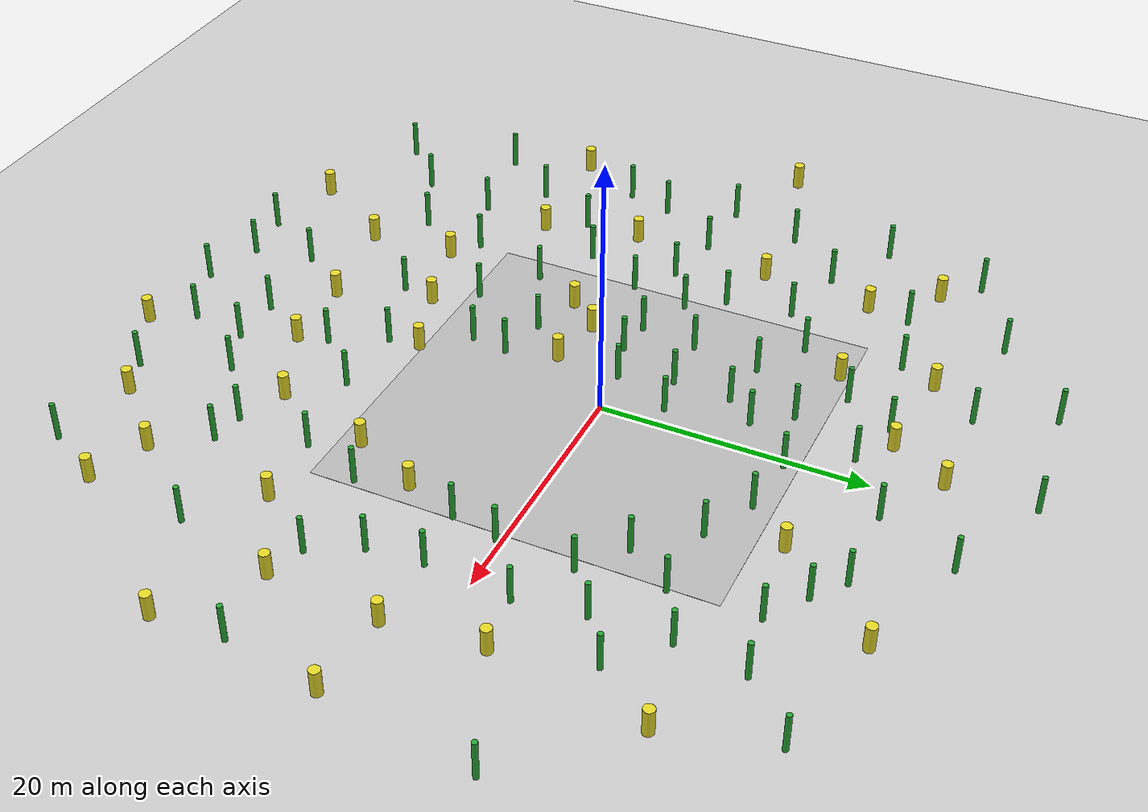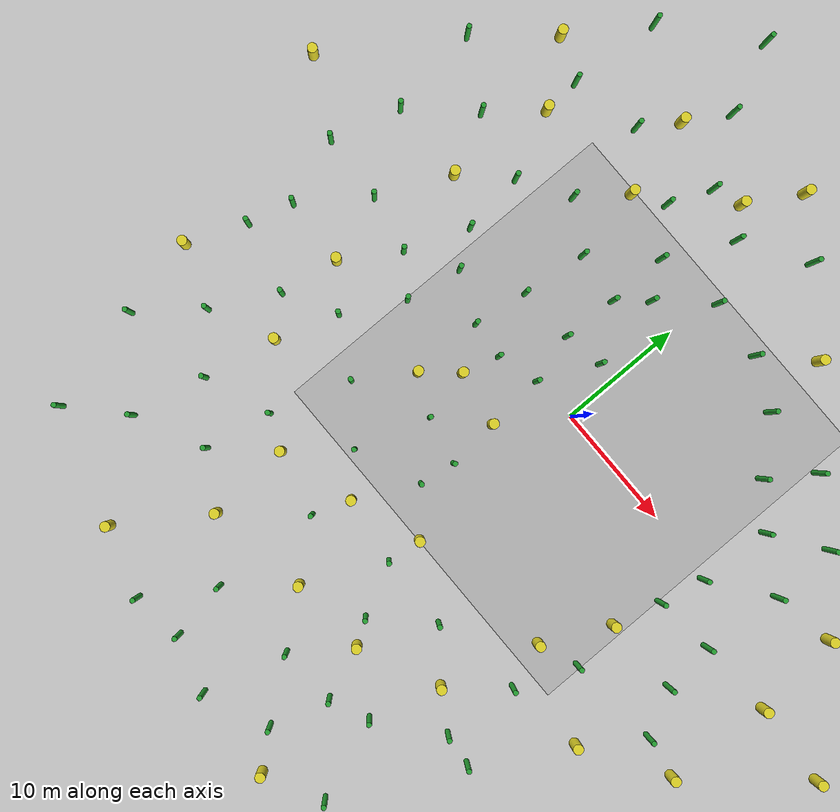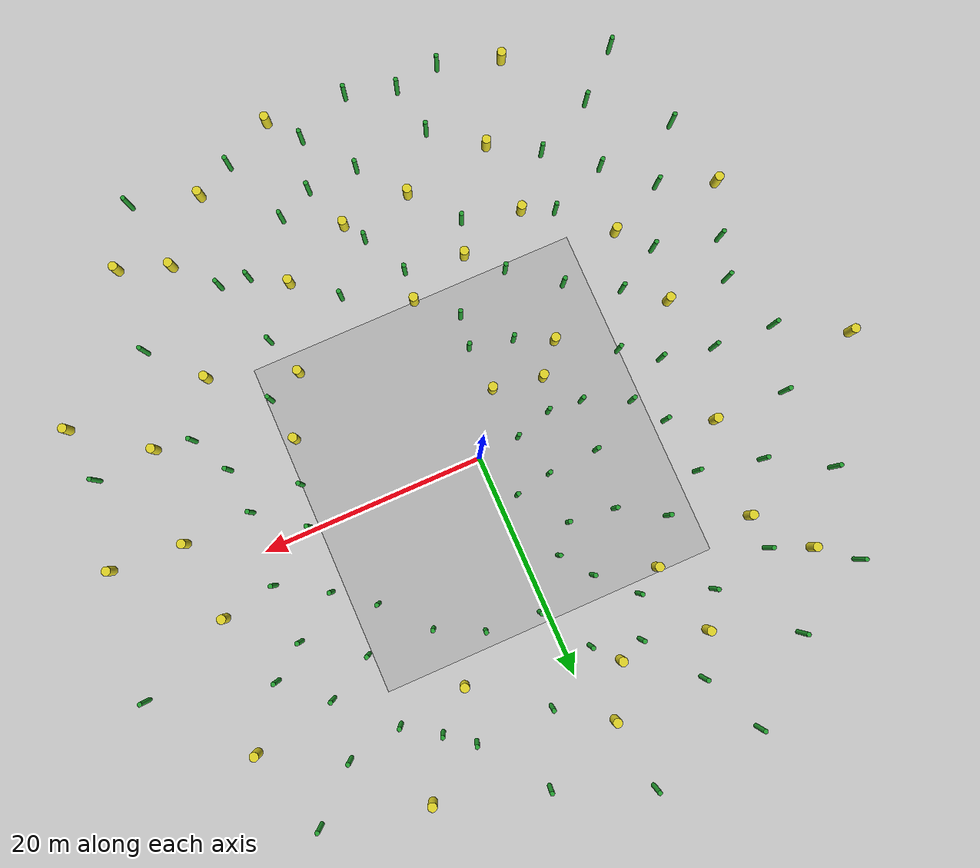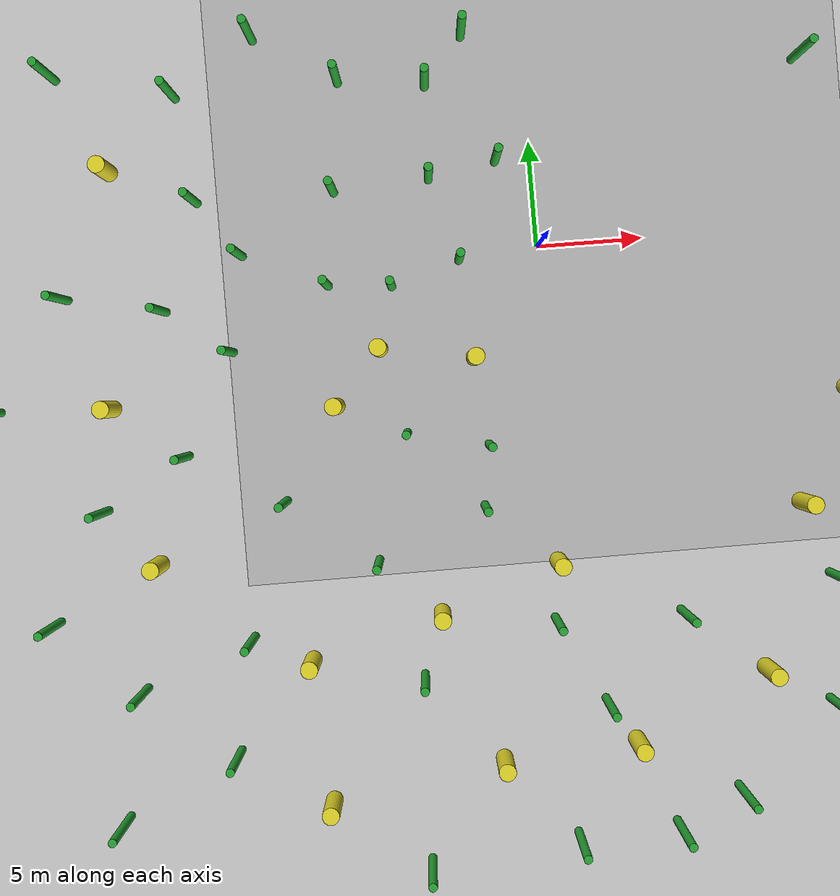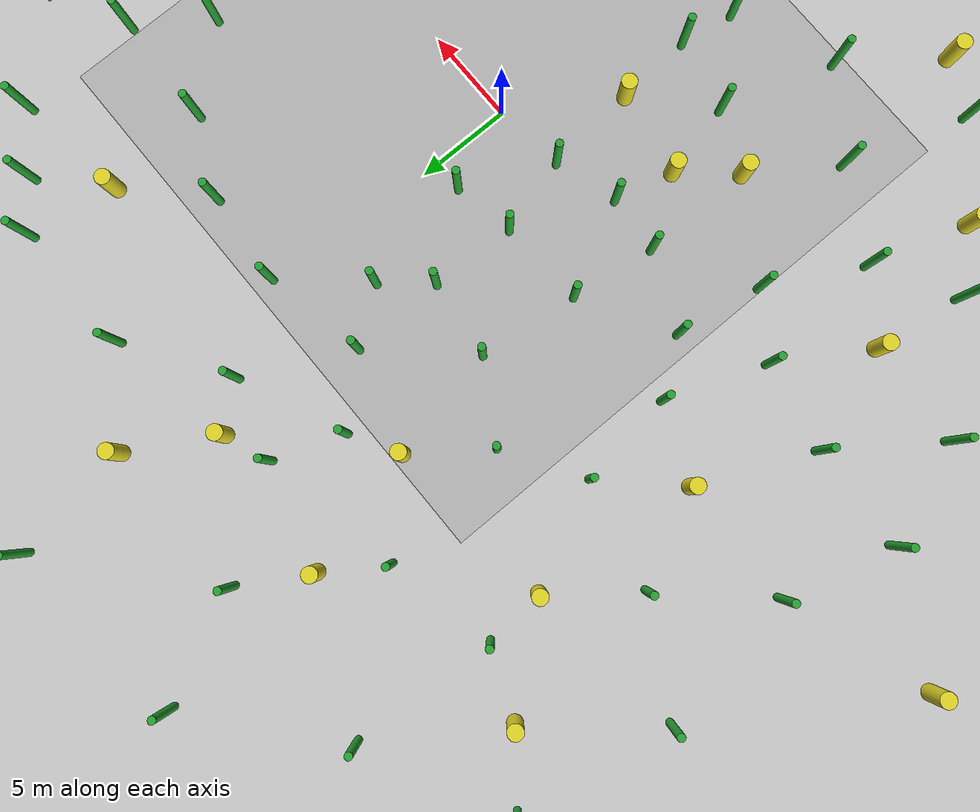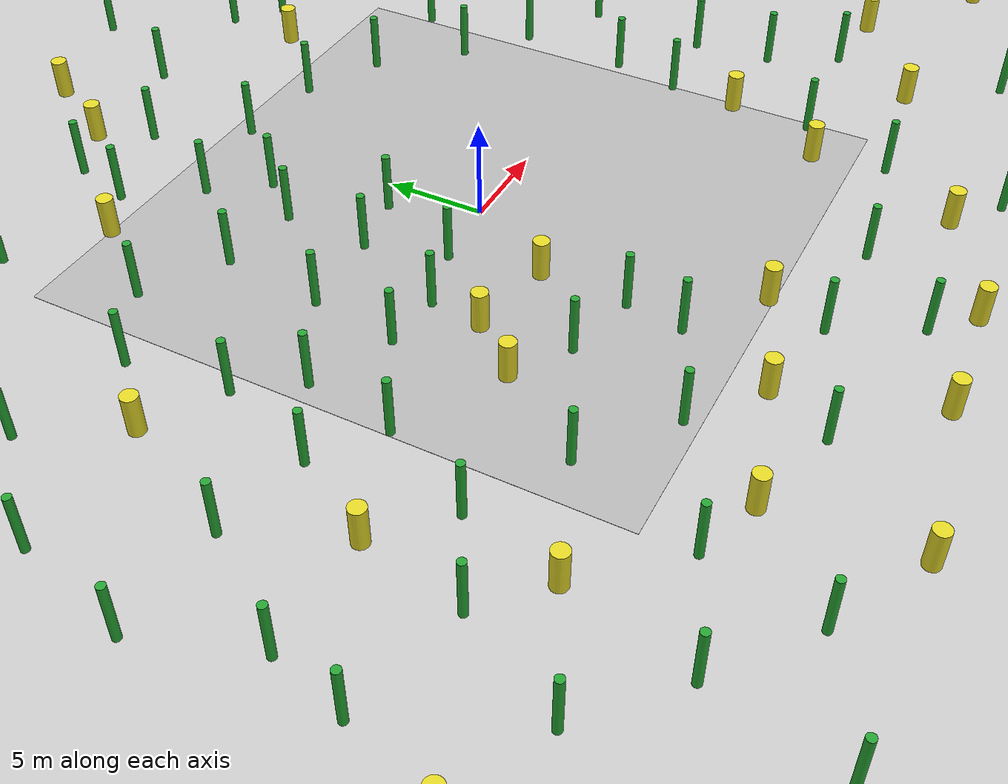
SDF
<sdf version="1.7">
 <world name="default">
  <physics type="ode">
   <ode>
    <solver>
     <type>quick</type>
     <iters>10</iters>
     <sor>1.3</sor>
     <use_dynamic_moi_rescaling>0</use_dynamic_moi_rescaling>
    </solver>
    <constraints>
     <cfm>0</cfm>
     <erp>0.2</erp>
     <contact_max_correcting_vel>100</contact_max_correcting_vel>
     <contact_surface_layer>0.001</contact_surface_layer>
    </constraints>
   </ode>
   <max_step_size>0.004</max_step_size>
   <real_time_factor>1</real_time_factor>
   <real_time_update_rate>250</real_time_update_rate>
  </physics>
  <light name="sun" type="directional">
   <cast_shadows>0</cast_shadows>
   <pose>0 0 100 0 -0 0</pose>
   <diffuse>0.8 0.8 0.8 1</diffuse>
   <specular>0.9 0.9 0.9 1</specular>
   <attenuation>
    <range>1000</range>
    <constant>0.9</constant>
    <linear>0.01</linear>
    <quadratic>0.001</quadratic>
   </attenuation>
   <direction>0.2 0.2 -0.9</direction>
   <spot><inner_angle>0</inner_angle><outer_angle>0</outer_angle><falloff>0</falloff></spot>
  </light>
  <model name="ground_plane">
   <static>1</static>
   <link name="link">
    <collision name="collision">
     <geometry><plane><normal>0 0 1</normal><size>100 100</size></plane></geometry>
     <surface>
      <contact><collide_bitmask>65535</collide_bitmask></contact>
      <friction><ode><mu>100</mu><mu2>50</mu2></ode></friction>
     </surface>
    </collision>
    <visual name="visual">
     <cast_shadows>0</cast_shadows>
     <geometry><plane><normal>0 0 1</normal><size>100 100</size></plane></geometry>
     <material>
      <script><uri>file://media/materials/scripts/gazebo.material</uri><name>Gazebo/Grey</name></script>
     </material>
    </visual>
   </link>
  </model>
  <model name="texture">
   <pose>-0.022154 0.017687 0 0 -0 0</pose>
   <static>1</static>
   <link name="prometheus_logo">
    <visual name="visual">
     <cast_shadows>0</cast_shadows>
     <geometry><box><size>30 30 0.01</size></box></geometry>
     <material>
      <script><uri>model://prometheus_texture/texture.material</uri><name>prometheus_logo2</name></script>
     </material>
    </visual>
   </link>
  </model>
  <model name="cylinder1">
   <pose>9.0226 19.85 0 0 -0 0</pose>
   <frame name="obs_cylinder_small::__model__" attached_to="obs_cylinder_small::link">
    <pose relative_to="__model__">3 0 1.5 0 -0 0</pose>
   </frame>
   <link name="obs_cylinder_small::link">
    <inertial><mass>1</mass></inertial>
    <pose relative_to="obs_cylinder_small::__model__">0 0 0 0 -0 0</pose>
    <visual name="visual">
     <geometry><cylinder><radius>0.2</radius><length>3</length></cylinder></geometry>
     <material>
      <script><name>Gazebo/Green</name><uri>file://media/materials/scripts/gazebo.material</uri></script>
     </material>
    </visual>
    <collision name="collision">
     <geometry><cylinder><radius>0.25</radius><length>3</length></cylinder></geometry>
    </collision>
   </link>
   <static>1</static>
  </model>
  <model name="cylinder7">
   <pose>-17.0526 -4.05651 0 0 -0 0</pose>
   <frame name="obs_cylinder_small::__model__" attached_to="obs_cylinder_small::link">
    <pose relative_to="__model__">7 3 1.5 0 -0 0</pose>
   </frame>
   <link name="obs_cylinder_small::link">
    <inertial><mass>1</mass></inertial>
    <pose relative_to="obs_cylinder_small::__model__">0 0 0 0 -0 0</pose>
    <visual name="visual">
     <geometry><cylinder><radius>0.2</radius><length>3</length></cylinder></geometry>
     <material>
      <script><name>Gazebo/Green</name><uri>file://media/materials/scripts/gazebo.material</uri></script>
     </material>
    </visual>
    <collision name="collision">
     <geometry><cylinder><radius>0.25</radius><length>3</length></cylinder></geometry>
    </collision>
   </link>
   <static>1</static>
  </model>
  <model name="cylinder8">
   <pose>-4.68562 -30.5584 0 0 -0 0</pose>
   <frame name="obs_cylinder_small::__model__" attached_to="obs_cylinder_small::link">
    <pose relative_to="__model__">9 3 2 0 -0 0</pose>
   </frame>
   <link name="obs_cylinder_small::link">
    <inertial><mass>1</mass></inertial>
    <pose relative_to="obs_cylinder_small::__model__">0 0 0 0 -0 0</pose>
    <visual name="visual">
     <geometry><cylinder><radius>0.2</radius><length>3</length></cylinder></geometry>
     <material>
      <script><name>Gazebo/Green</name><uri>file://media/materials/scripts/gazebo.material</uri></script>
     </material>
    </visual>
    <collision name="collision">
     <geometry><cylinder><radius>0.25</radius><length>3</length></cylinder></geometry>
    </collision>
   </link>
   <static>1</static>
  </model>
  <model name="cylinder9">
   <pose>8.9225 5.15263 0 0 -0 0</pose>
   <frame name="obs_cylinder_small::__model__" attached_to="obs_cylinder_small::link">
    <pose relative_to="__model__">11 3 2 0 -0 0</pose>
   </frame>
   <link name="obs_cylinder_small::link">
    <inertial><mass>1</mass></inertial>
    <pose relative_to="obs_cylinder_small::__model__">0 0 0 0 -0 0</pose>
    <visual name="visual">
     <geometry><cylinder><radius>0.2</radius><length>3</length></cylinder></geometry>
     <material>
      <script><name>Gazebo/Green</name><uri>file://media/materials/scripts/gazebo.material</uri></script>
     </material>
    </visual>
    <collision name="collision">
     <geometry><cylinder><radius>0.25</radius><length>3</length></cylinder></geometry>
    </collision>
   </link>
   <static>1</static>
  </model>
  <model name="cylinder2">
   <pose>-12.6689 13.8388 0 0 -0 0</pose>
   <frame name="obs_cylinder_small::__model__" attached_to="obs_cylinder_small::link">
    <pose relative_to="__model__">5 2 2 0 -0 0</pose>
   </frame>
   <link name="obs_cylinder_small::link">
    <inertial><mass>1</mass></inertial>
    <pose relative_to="obs_cylinder_small::__model__">0 0 0 0 -0 0</pose>
    <visual name="visual">
     <geometry><cylinder><radius>0.2</radius><length>3</length></cylinder></geometry>
     <material>
      <script><name>Gazebo/Green</name><uri>file://media/materials/scripts/gazebo.material</uri></script>
     </material>
    </visual>
    <collision name="collision">
     <geometry><cylinder><radius>0.25</radius><length>3</length></cylinder></geometry>
    </collision>
   </link>
   <static>1</static>
  </model>
  <model name="cylinder3">
   <pose>7.1434 -20.5448 0 0 -0 0</pose>
   <frame name="obs_cylinder_small::__model__" attached_to="obs_cylinder_small::link">
    <pose relative_to="__model__">5 -2 1.5 0 -0 0</pose>
   </frame>
   <link name="obs_cylinder_small::link">
    <inertial><mass>1</mass></inertial>
    <pose relative_to="obs_cylinder_small::__model__">0 0 0 0 -0 0</pose>
    <visual name="visual">
     <geometry><cylinder><radius>0.2</radius><length>3</length></cylinder></geometry>
     <material>
      <script><name>Gazebo/Green</name><uri>file://media/materials/scripts/gazebo.material</uri></script>
     </material>
    </visual>
    <collision name="collision">
     <geometry><cylinder><radius>0.25</radius><length>3</length></cylinder></geometry>
    </collision>
   </link>
   <static>1</static>
  </model>
  <model name="cylinder4">
   <pose>-15.8569 -1.65671 0 0 -0 0</pose>
   <frame name="obs_cylinder_small::__model__" attached_to="obs_cylinder_small::link">
    <pose relative_to="__model__">-2 0 1.5 0 -0 0</pose>
   </frame>
   <link name="obs_cylinder_small::link">
    <inertial><mass>1</mass></inertial>
    <pose relative_to="obs_cylinder_small::__model__">0 0 0 0 -0 0</pose>
    <visual name="visual">
     <geometry><cylinder><radius>0.2</radius><length>3</length></cylinder></geometry>
     <material>
      <script><name>Gazebo/Green</name><uri>file://media/materials/scripts/gazebo.material</uri></script>
     </material>
    </visual>
    <collision name="collision">
     <geometry><cylinder><radius>0.25</radius><length>3</length></cylinder></geometry>
    </collision>
   </link>
   <static>1</static>
  </model>
  <model name="cylinder5">
   <pose>0.10423 1.60114 0 0 -0 0</pose>
   <frame name="obs_cylinder_small::__model__" attached_to="obs_cylinder_small::link">
    <pose relative_to="__model__">-5 2 1.5 0 -0 0</pose>
   </frame>
   <link name="obs_cylinder_small::link">
    <inertial><mass>1</mass></inertial>
    <pose relative_to="obs_cylinder_small::__model__">0 0 0 0 -0 0</pose>
    <visual name="visual">
     <geometry><cylinder><radius>0.2</radius><length>3</length></cylinder></geometry>
     <material>
      <script><name>Gazebo/Green</name><uri>file://media/materials/scripts/gazebo.material</uri></script>
     </material>
    </visual>
    <collision name="collision">
     <geometry><cylinder><radius>0.25</radius><length>3</length></cylinder></geometry>
    </collision>
   </link>
   <static>1</static>
  </model>
  <model name="cylinder6">
   <pose>-2.04873 0.66566 0 0 -0 0</pose>
   <frame name="obs_cylinder_small::__model__" attached_to="obs_cylinder_small::link">
    <pose relative_to="__model__">-5 -2 1.5 0 -0 0</pose>
   </frame>
   <link name="obs_cylinder_small::link">
    <inertial><mass>1</mass></inertial>
    <pose relative_to="obs_cylinder_small::__model__">0 0 0 0 -0 0</pose>
    <visual name="visual">
     <geometry><cylinder><radius>0.2</radius><length>3</length></cylinder></geometry>
     <material>
      <script><name>Gazebo/Green</name><uri>file://media/materials/scripts/gazebo.material</uri></script>
     </material>
    </visual>
    <collision name="collision">
     <geometry><cylinder><radius>0.25</radius><length>3</length></cylinder></geometry>
    </collision>
   </link>
   <static>1</static>
  </model>
  <model name="cylinder4_clone_0">
   <pose>-0.85021 6.24417 0 0 -0 0</pose>
   <frame name="obs_cylinder_small::__model__" attached_to="obs_cylinder_small::link">
    <pose relative_to="__model__">-1.97992 4.00703 1.5 0 -0 0</pose>
   </frame>
   <link name="obs_cylinder_small::link">
    <inertial><mass>1</mass></inertial>
    <pose relative_to="obs_cylinder_small::__model__">0 0 0 0 -0 0</pose>
    <visual name="visual">
     <geometry><cylinder><radius>0.2</radius><length>3</length></cylinder></geometry>
     <material>
      <script><name>Gazebo/Green</name><uri>file://media/materials/scripts/gazebo.material</uri></script>
     </material>
    </visual>
    <collision name="collision">
     <geometry><cylinder><radius>0.25</radius><length>3</length></cylinder></geometry>
    </collision>
   </link>
   <static>1</static>
  </model>
  <model name="cylinder4_clone_1">
   <pose>-1.81173 1.66661 0 0 -0 0</pose>
   <frame name="obs_cylinder_small::__model__" attached_to="obs_cylinder_small::link">
    <pose relative_to="__model__">-1.9564 -2.0159 1.5 0 -0 0</pose>
   </frame>
   <link name="obs_cylinder_small::link">
    <inertial><mass>1</mass></inertial>
    <pose relative_to="obs_cylinder_small::__model__">0 0 0 0 -0 0</pose>
    <visual name="visual">
     <geometry><cylinder><radius>0.2</radius><length>3</length></cylinder></geometry>
     <material>
      <script><name>Gazebo/Green</name><uri>file://media/materials/scripts/gazebo.material</uri></script>
     </material>
    </visual>
    <collision name="collision">
     <geometry><cylinder><radius>0.25</radius><length>3</length></cylinder></geometry>
    </collision>
   </link>
   <static>1</static>
  </model>
  <model name="cylinder4_clone_10">
   <pose>14.9292 -7.18549 0 0 -0 0</pose>
   <frame name="obs_cylinder_small::__model__" attached_to="obs_cylinder_small::link">
    <pose relative_to="__model__">7.0065 -4.01751 1.5 0 -0 0</pose>
   </frame>
   <link name="obs_cylinder_small::link">
    <inertial><mass>1</mass></inertial>
    <pose relative_to="obs_cylinder_small::__model__">0 0 0 0 -0 0</pose>
    <visual name="visual">
     <geometry><cylinder><radius>0.2</radius><length>3</length></cylinder></geometry>
     <material>
      <script><name>Gazebo/Green</name><uri>file://media/materials/scripts/gazebo.material</uri></script>
     </material>
    </visual>
    <collision name="collision">
     <geometry><cylinder><radius>0.25</radius><length>3</length></cylinder></geometry>
    </collision>
   </link>
   <static>1</static>
  </model>
  <model name="cylinder4_clone_11">
   <pose>-18.5022 3.2621 0 0 -0 0</pose>
   <frame name="obs_cylinder_small::__model__" attached_to="obs_cylinder_small::link">
    <pose relative_to="__model__">9.0654 0.083267 1.5 0 -0 0</pose>
   </frame>
   <link name="obs_cylinder_small::link">
    <inertial><mass>1</mass></inertial>
    <pose relative_to="obs_cylinder_small::__model__">0 0 0 0 -0 0</pose>
    <visual name="visual">
     <geometry><cylinder><radius>0.2</radius><length>3</length></cylinder></geometry>
     <material>
      <script><name>Gazebo/Green</name><uri>file://media/materials/scripts/gazebo.material</uri></script>
     </material>
    </visual>
    <collision name="collision">
     <geometry><cylinder><radius>0.25</radius><length>3</length></cylinder></geometry>
    </collision>
   </link>
   <static>1</static>
  </model>
  <model name="cylinder4_clone_12">
   <pose>24.5866 10.4494 0 0 -0 0</pose>
   <frame name="obs_cylinder_small::__model__" attached_to="obs_cylinder_small::link">
    <pose relative_to="__model__">9.0896 -2.91154 1.5 0 -0 0</pose>
   </frame>
   <link name="obs_cylinder_small::link">
    <inertial><mass>1</mass></inertial>
    <pose relative_to="obs_cylinder_small::__model__">0 0 0 0 -0 0</pose>
    <visual name="visual">
     <geometry><cylinder><radius>0.2</radius><length>3</length></cylinder></geometry>
     <material>
      <script><name>Gazebo/Green</name><uri>file://media/materials/scripts/gazebo.material</uri></script>
     </material>
    </visual>
    <collision name="collision">
     <geometry><cylinder><radius>0.25</radius><length>3</length></cylinder></geometry>
    </collision>
   </link>
   <static>1</static>
  </model>
  <model name="cylinder4_clone_13">
   <pose>-1.50814 -19.6511 0 0 -0 0</pose>
   <frame name="obs_cylinder_small::__model__" attached_to="obs_cylinder_small::link">
    <pose relative_to="__model__">3.01135 -2.03851 1.5 0 -0 0</pose>
   </frame>
   <link name="obs_cylinder_small::link">
    <inertial><mass>1</mass></inertial>
    <pose relative_to="obs_cylinder_small::__model__">0 0 0 0 -0 0</pose>
    <visual name="visual">
     <geometry><cylinder><radius>0.2</radius><length>3</length></cylinder></geometry>
     <material>
      <script><name>Gazebo/Green</name><uri>file://media/materials/scripts/gazebo.material</uri></script>
     </material>
    </visual>
    <collision name="collision">
     <geometry><cylinder><radius>0.25</radius><length>3</length></cylinder></geometry>
    </collision>
   </link>
   <static>1</static>
  </model>
  <model name="cylinder4_clone_14">
   <pose>-6.05536 15.1916 0 0 -0 0</pose>
   <frame name="obs_cylinder_large::__model__" attached_to="obs_cylinder_large::link">
    <pose relative_to="__model__">2.02671 5.11168 1.5 0 -0 0</pose>
   </frame>
   <link name="obs_cylinder_large::link">
    <inertial><mass>1</mass></inertial>
    <pose relative_to="obs_cylinder_large::__model__">0 0 0 0 -0 0</pose>
    <visual name="visual">
     <geometry><cylinder><radius>0.4</radius><length>2</length></cylinder></geometry>
     <material>
      <script><name>Gazebo/Yellow</name><uri>file://media/materials/scripts/gazebo.material</uri></script>
     </material>
    </visual>
    <collision name="collision">
     <geometry><cylinder><radius>0.25</radius><length>2</length></cylinder></geometry>
    </collision>
   </link>
   <static>1</static>
  </model>
  <model name="cylinder4_clone_15">
   <pose>29.4346 -21.4647 0 0 -0 0</pose>
   <frame name="obs_cylinder_large::__model__" attached_to="obs_cylinder_large::link">
    <pose relative_to="__model__">2.02671 5.11168 1.5 0 -0 0</pose>
   </frame>
   <link name="obs_cylinder_large::link">
    <inertial><mass>1</mass></inertial>
    <pose relative_to="obs_cylinder_large::__model__">0 0 0 0 -0 0</pose>
    <visual name="visual">
     <geometry><cylinder><radius>0.4</radius><length>2</length></cylinder></geometry>
     <material>
      <script><name>Gazebo/Yellow</name><uri>file://media/materials/scripts/gazebo.material</uri></script>
     </material>
    </visual>
    <collision name="collision">
     <geometry><cylinder><radius>0.25</radius><length>2</length></cylinder></geometry>
    </collision>
   </link>
   <static>1</static>
  </model>
  <model name="cylinder4_clone_16">
   <pose>-13.3105 21.4087 0 0 -0 0</pose>
   <frame name="obs_cylinder_large::__model__" attached_to="obs_cylinder_large::link">
    <pose relative_to="__model__">1.547 -0.460893 1.5 0 -0 0</pose>
   </frame>
   <link name="obs_cylinder_large::link">
    <inertial><mass>1</mass></inertial>
    <pose relative_to="obs_cylinder_large::__model__">0 0 0 0 -0 0</pose>
    <visual name="visual">
     <geometry><cylinder><radius>0.4</radius><length>2</length></cylinder></geometry>
     <material>
      <script><name>Gazebo/Yellow</name><uri>file://media/materials/scripts/gazebo.material</uri></script>
     </material>
    </visual>
    <collision name="collision">
     <geometry><cylinder><radius>0.25</radius><length>2</length></cylinder></geometry>
    </collision>
   </link>
   <static>1</static>
  </model>
  <model name="cylinder4_clone_17">
   <pose>-2.4282 -1.09738 0 0 -0 0</pose>
   <frame name="obs_cylinder_large::__model__" attached_to="obs_cylinder_large::link">
    <pose relative_to="__model__">-1.00318 -3.92453 1.5 0 -0 0</pose>
   </frame>
   <link name="obs_cylinder_large::link">
    <inertial><mass>1</mass></inertial>
    <pose relative_to="obs_cylinder_large::__model__">0 0 0 0 -0 0</pose>
    <visual name="visual">
     <geometry><cylinder><radius>0.4</radius><length>2</length></cylinder></geometry>
     <material>
      <script><name>Gazebo/Yellow</name><uri>file://media/materials/scripts/gazebo.material</uri></script>
     </material>
    </visual>
    <collision name="collision">
     <geometry><cylinder><radius>0.25</radius><length>2</length></cylinder></geometry>
    </collision>
   </link>
   <static>1</static>
  </model>
  <model name="cylinder4_clone_18">
   <pose>-3.87392 -0.35835 0 0 -0 0</pose>
   <frame name="obs_cylinder_large::__model__" attached_to="obs_cylinder_large::link">
    <pose relative_to="__model__">-3.97554 -3.89536 1.5 0 -0 0</pose>
   </frame>
   <link name="obs_cylinder_large::link">
    <inertial><mass>1</mass></inertial>
    <pose relative_to="obs_cylinder_large::__model__">0 0 0 0 -0 0</pose>
    <visual name="visual">
     <geometry><cylinder><radius>0.4</radius><length>2</length></cylinder></geometry>
     <material>
      <script><name>Gazebo/Yellow</name><uri>file://media/materials/scripts/gazebo.material</uri></script>
     </material>
    </visual>
    <collision name="collision">
     <geometry><cylinder><radius>0.25</radius><length>2</length></cylinder></geometry>
    </collision>
   </link>
   <static>1</static>
  </model>
  <model name="cylinder4_clone_19">
   <pose>9.35839 -34.1114 0 0 -0 0</pose>
   <frame name="obs_cylinder_large::__model__" attached_to="obs_cylinder_large::link">
    <pose relative_to="__model__">-4.01198 -0.900726 1.5 0 -0 0</pose>
   </frame>
   <link name="obs_cylinder_large::link">
    <inertial><mass>1</mass></inertial>
    <pose relative_to="obs_cylinder_large::__model__">0 0 0 0 -0 0</pose>
    <visual name="visual">
     <geometry><cylinder><radius>0.4</radius><length>2</length></cylinder></geometry>
     <material>
      <script><name>Gazebo/Yellow</name><uri>file://media/materials/scripts/gazebo.material</uri></script>
     </material>
    </visual>
    <collision name="collision">
     <geometry><cylinder><radius>0.25</radius><length>2</length></cylinder></geometry>
    </collision>
   </link>
   <static>1</static>
  </model>
  <model name="cylinder4_clone_20">
   <pose>-29.9379 -1.49916 0 0 -0 0</pose>
   <frame name="obs_cylinder_large::__model__" attached_to="obs_cylinder_large::link">
    <pose relative_to="__model__">-3.99798 4.28559 1.5 0 -0 0</pose>
   </frame>
   <link name="obs_cylinder_large::link">
    <inertial><mass>1</mass></inertial>
    <pose relative_to="obs_cylinder_large::__model__">0 0 0 0 -0 0</pose>
    <visual name="visual">
     <geometry><cylinder><radius>0.4</radius><length>2</length></cylinder></geometry>
     <material>
      <script><name>Gazebo/Yellow</name><uri>file://media/materials/scripts/gazebo.material</uri></script>
     </material>
    </visual>
    <collision name="collision">
     <geometry><cylinder><radius>0.25</radius><length>2</length></cylinder></geometry>
    </collision>
   </link>
   <static>1</static>
  </model>
  <model name="cylinder4_clone_3">
   <pose>-5.90099 -14.8686 0 0 -0 0</pose>
   <frame name="obs_cylinder_large::__model__" attached_to="obs_cylinder_large::link">
    <pose relative_to="__model__">-0.02147 -2 1.5 0 -0 0</pose>
   </frame>
   <link name="obs_cylinder_large::link">
    <inertial><mass>1</mass></inertial>
    <pose relative_to="obs_cylinder_large::__model__">0 0 0 0 -0 0</pose>
    <visual name="visual">
     <geometry><cylinder><radius>0.4</radius><length>2</length></cylinder></geometry>
     <material>
      <script><name>Gazebo/Yellow</name><uri>file://media/materials/scripts/gazebo.material</uri></script>
     </material>
    </visual>
    <collision name="collision">
     <geometry><cylinder><radius>0.25</radius><length>2</length></cylinder></geometry>
    </collision>
   </link>
   <static>1</static>
  </model>
  <model name="cylinder4_clone_4">
   <pose>30.5165 -5.67243 0 0 -0 0</pose>
   <frame name="obs_cylinder_large::__model__" attached_to="obs_cylinder_large::link">
    <pose relative_to="__model__">1.91528 1.99383 1.5 0 -0 0</pose>
   </frame>
   <link name="obs_cylinder_large::link">
    <inertial><mass>1</mass></inertial>
    <pose relative_to="obs_cylinder_large::__model__">0 0 0 0 -0 0</pose>
    <visual name="visual">
     <geometry><cylinder><radius>0.4</radius><length>2</length></cylinder></geometry>
     <material>
      <script><name>Gazebo/Yellow</name><uri>file://media/materials/scripts/gazebo.material</uri></script>
     </material>
    </visual>
    <collision name="collision">
     <geometry><cylinder><radius>0.25</radius><length>2</length></cylinder></geometry>
    </collision>
   </link>
   <static>1</static>
  </model>
  <model name="cylinder4_clone_5">
   <pose>-14.066 -10.7554 0 0 -0 0</pose>
   <frame name="obs_cylinder_large::__model__" attached_to="obs_cylinder_large::link">
    <pose relative_to="__model__">3.98158 3.97316 1.5 0 -0 0</pose>
   </frame>
   <link name="obs_cylinder_large::link">
    <inertial><mass>1</mass></inertial>
    <pose relative_to="obs_cylinder_large::__model__">0 0 0 0 -0 0</pose>
    <visual name="visual">
     <geometry><cylinder><radius>0.4</radius><length>2</length></cylinder></geometry>
     <material>
      <script><name>Gazebo/Yellow</name><uri>file://media/materials/scripts/gazebo.material</uri></script>
     </material>
    </visual>
    <collision name="collision">
     <geometry><cylinder><radius>0.25</radius><length>2</length></cylinder></geometry>
    </collision>
   </link>
   <static>1</static>
  </model>
  <model name="cylinder3_clone">
   <pose>5.25573 -13.1614 0 0 -0 0</pose>
   <frame name="obs_cylinder_large::__model__" attached_to="obs_cylinder_large::link">
    <pose relative_to="__model__">6.07287 0.13588 1.5 0 -0 0</pose>
   </frame>
   <link name="obs_cylinder_large::link">
    <inertial><mass>1</mass></inertial>
    <pose relative_to="obs_cylinder_large::__model__">0 0 0 0 -0 0</pose>
    <visual name="visual">
     <geometry><cylinder><radius>0.4</radius><length>2</length></cylinder></geometry>
     <material>
      <script><name>Gazebo/Yellow</name><uri>file://media/materials/scripts/gazebo.material</uri></script>
     </material>
    </visual>
    <collision name="collision">
     <geometry><cylinder><radius>0.25</radius><length>2</length></cylinder></geometry>
    </collision>
   </link>
   <static>1</static>
  </model>
  <model name="cylinder3_clone_0">
   <pose>-4.43676 -10.8165 0 0 -0 0</pose>
   <frame name="obs_cylinder_large::__model__" attached_to="obs_cylinder_large::link">
    <pose relative_to="__model__">4.15022 -4.06495 1.5 0 -0 0</pose>
   </frame>
   <link name="obs_cylinder_large::link">
    <inertial><mass>1</mass></inertial>
    <pose relative_to="obs_cylinder_large::__model__">0 0 0 0 -0 0</pose>
    <visual name="visual">
     <geometry><cylinder><radius>0.4</radius><length>2</length></cylinder></geometry>
     <material>
      <script><name>Gazebo/Yellow</name><uri>file://media/materials/scripts/gazebo.material</uri></script>
     </material>
    </visual>
    <collision name="collision">
     <geometry><cylinder><radius>0.25</radius><length>2</length></cylinder></geometry>
    </collision>
   </link>
   <static>1</static>
  </model>
  <model name="cylinder3_clone_1">
   <pose>-20.2103 -17.6268 0 0 -0 0</pose>
   <frame name="obs_cylinder_large::__model__" attached_to="obs_cylinder_large::link">
    <pose relative_to="__model__">8.06445 -0.95966 1.5 0 -0 0</pose>
   </frame>
   <link name="obs_cylinder_large::link">
    <inertial><mass>1</mass></inertial>
    <pose relative_to="obs_cylinder_large::__model__">0 0 0 0 -0 0</pose>
    <visual name="visual">
     <geometry><cylinder><radius>0.4</radius><length>2</length></cylinder></geometry>
     <material>
      <script><name>Gazebo/Yellow</name><uri>file://media/materials/scripts/gazebo.material</uri></script>
     </material>
    </visual>
    <collision name="collision">
     <geometry><cylinder><radius>0.25</radius><length>2</length></cylinder></geometry>
    </collision>
   </link>
   <static>1</static>
  </model>
  <model name="cylinder3_clone_10">
   <pose>6.88579 -25.7884 0 0 -0 0</pose>
   <frame name="obs_cylinder_small::__model__" attached_to="obs_cylinder_small::link">
    <pose relative_to="__model__">3.03343 -6.9094 1.5 0 -0 0</pose>
   </frame>
   <link name="obs_cylinder_small::link">
    <inertial><mass>1</mass></inertial>
    <pose relative_to="obs_cylinder_small::__model__">0 0 0 0 -0 0</pose>
    <visual name="visual">
     <geometry><cylinder><radius>0.2</radius><length>3</length></cylinder></geometry>
     <material>
      <script><name>Gazebo/Green</name><uri>file://media/materials/scripts/gazebo.material</uri></script>
     </material>
    </visual>
    <collision name="collision">
     <geometry><cylinder><radius>0.25</radius><length>3</length></cylinder></geometry>
    </collision>
   </link>
   <static>1</static>
  </model>
  <model name="cylinder3_clone_11">
   <pose>-2.50895 -6.24666 0 0 -0 0</pose>
   <frame name="obs_cylinder_small::__model__" attached_to="obs_cylinder_small::link">
    <pose relative_to="__model__">-0.97445 -5.80554 1.5 0 -0 0</pose>
   </frame>
   <link name="obs_cylinder_small::link">
    <inertial><mass>1</mass></inertial>
    <pose relative_to="obs_cylinder_small::__model__">0 0 0 0 -0 0</pose>
    <visual name="visual">
     <geometry><cylinder><radius>0.2</radius><length>3</length></cylinder></geometry>
     <material>
      <script><name>Gazebo/Green</name><uri>file://media/materials/scripts/gazebo.material</uri></script>
     </material>
    </visual>
    <collision name="collision">
     <geometry><cylinder><radius>0.25</radius><length>3</length></cylinder></geometry>
    </collision>
   </link>
   <static>1</static>
  </model>
  <model name="cylinder3_clone_12">
   <pose>-0.01069 -3.15762 0 0 -0 0</pose>
   <frame name="obs_cylinder_small::__model__" attached_to="obs_cylinder_small::link">
    <pose relative_to="__model__">-3.04238 -6.01581 1.5 0 -0 0</pose>
   </frame>
   <link name="obs_cylinder_small::link">
    <inertial><mass>1</mass></inertial>
    <pose relative_to="obs_cylinder_small::__model__">0 0 0 0 -0 0</pose>
    <visual name="visual">
     <geometry><cylinder><radius>0.2</radius><length>3</length></cylinder></geometry>
     <material>
      <script><name>Gazebo/Green</name><uri>file://media/materials/scripts/gazebo.material</uri></script>
     </material>
    </visual>
    <collision name="collision">
     <geometry><cylinder><radius>0.25</radius><length>3</length></cylinder></geometry>
    </collision>
   </link>
   <static>1</static>
  </model>
  <model name="cylinder3_clone_13">
   <pose>-1.88921 -3.28731 0 0 -0 0</pose>
   <frame name="obs_cylinder_small::__model__" attached_to="obs_cylinder_small::link">
    <pose relative_to="__model__">-4.97933 -5.0259 1.5 0 -0 0</pose>
   </frame>
   <link name="obs_cylinder_small::link">
    <inertial><mass>1</mass></inertial>
    <pose relative_to="obs_cylinder_small::__model__">0 0 0 0 -0 0</pose>
    <visual name="visual">
     <geometry><cylinder><radius>0.2</radius><length>3</length></cylinder></geometry>
     <material>
      <script><name>Gazebo/Green</name><uri>file://media/materials/scripts/gazebo.material</uri></script>
     </material>
    </visual>
    <collision name="collision">
     <geometry><cylinder><radius>0.25</radius><length>3</length></cylinder></geometry>
    </collision>
   </link>
   <static>1</static>
  </model>
  <model name="cylinder3_clone_14">
   <pose>6.8163 2.89267 0 0 -0 0</pose>
   <frame name="obs_cylinder_small::__model__" attached_to="obs_cylinder_small::link">
    <pose relative_to="__model__">5.96757 5.00455 1.5 0 -0 0</pose>
   </frame>
   <link name="obs_cylinder_small::link">
    <inertial><mass>1</mass></inertial>
    <pose relative_to="obs_cylinder_small::__model__">0 0 0 0 -0 0</pose>
    <visual name="visual">
     <geometry><cylinder><radius>0.2</radius><length>3</length></cylinder></geometry>
     <material>
      <script><name>Gazebo/Green</name><uri>file://media/materials/scripts/gazebo.material</uri></script>
     </material>
    </visual>
    <collision name="collision">
     <geometry><cylinder><radius>0.25</radius><length>3</length></cylinder></geometry>
    </collision>
   </link>
   <static>1</static>
  </model>
  <model name="cylinder3_clone_2">
   <pose>-9.20412 20.1685 0 0 -0 0</pose>
   <frame name="obs_cylinder_small::__model__" attached_to="obs_cylinder_small::link">
    <pose relative_to="__model__">7.01908 -1.94151 1.5 0 -0 0</pose>
   </frame>
   <link name="obs_cylinder_small::link">
    <inertial><mass>1</mass></inertial>
    <pose relative_to="obs_cylinder_small::__model__">0 0 0 0 -0 0</pose>
    <visual name="visual">
     <geometry><cylinder><radius>0.2</radius><length>3</length></cylinder></geometry>
     <material>
      <script><name>Gazebo/Green</name><uri>file://media/materials/scripts/gazebo.material</uri></script>
     </material>
    </visual>
    <collision name="collision">
     <geometry><cylinder><radius>0.25</radius><length>3</length></cylinder></geometry>
    </collision>
   </link>
   <static>1</static>
  </model>
  <model name="cylinder3_clone_3">
   <pose>-12.6791 -29.8524 0 0 -0 0</pose>
   <frame name="obs_cylinder_small::__model__" attached_to="obs_cylinder_small::link">
    <pose relative_to="__model__">2.02255 -4.00149 1.5 0 -0 0</pose>
   </frame>
   <link name="obs_cylinder_small::link">
    <inertial><mass>1</mass></inertial>
    <pose relative_to="obs_cylinder_small::__model__">0 0 0 0 -0 0</pose>
    <visual name="visual">
     <geometry><cylinder><radius>0.2</radius><length>3</length></cylinder></geometry>
     <material>
      <script><name>Gazebo/Green</name><uri>file://media/materials/scripts/gazebo.material</uri></script>
     </material>
    </visual>
    <collision name="collision">
     <geometry><cylinder><radius>0.25</radius><length>3</length></cylinder></geometry>
    </collision>
   </link>
   <static>1</static>
  </model>
  <model name="cylinder3_clone_4">
   <pose>-13.0228 -13.1395 0 0 -0 0</pose>
   <frame name="obs_cylinder_small::__model__" attached_to="obs_cylinder_small::link">
    <pose relative_to="__model__">0.17873 2.05724 1.5 0 -0 0</pose>
   </frame>
   <link name="obs_cylinder_small::link">
    <inertial><mass>1</mass></inertial>
    <pose relative_to="obs_cylinder_small::__model__">0 0 0 0 -0 0</pose>
    <visual name="visual">
     <geometry><cylinder><radius>0.2</radius><length>3</length></cylinder></geometry>
     <material>
      <script><name>Gazebo/Green</name><uri>file://media/materials/scripts/gazebo.material</uri></script>
     </material>
    </visual>
    <collision name="collision">
     <geometry><cylinder><radius>0.25</radius><length>3</length></cylinder></geometry>
    </collision>
   </link>
   <static>1</static>
  </model>
  <model name="cylinder3_clone_5">
   <pose>0.16806 2.09006 0 0 -0 0</pose>
   <frame name="obs_cylinder_small::__model__" attached_to="obs_cylinder_small::link">
    <pose relative_to="__model__">-1.85729 2.09778 1.5 0 -0 0</pose>
   </frame>
   <link name="obs_cylinder_small::link">
    <inertial><mass>1</mass></inertial>
    <pose relative_to="obs_cylinder_small::__model__">0 0 0 0 -0 0</pose>
    <visual name="visual">
     <geometry><cylinder><radius>0.2</radius><length>3</length></cylinder></geometry>
     <material>
      <script><name>Gazebo/Green</name><uri>file://media/materials/scripts/gazebo.material</uri></script>
     </material>
    </visual>
    <collision name="collision">
     <geometry><cylinder><radius>0.25</radius><length>3</length></cylinder></geometry>
    </collision>
   </link>
   <static>1</static>
  </model>
  <model name="cylinder3_clone_6">
   <pose>-13.3371 -9.62586 0 0 -0 0</pose>
   <frame name="obs_cylinder_small::__model__" attached_to="obs_cylinder_small::link">
    <pose relative_to="__model__">-3.98585 1.05791 1.5 0 -0 0</pose>
   </frame>
   <link name="obs_cylinder_small::link">
    <inertial><mass>1</mass></inertial>
    <pose relative_to="obs_cylinder_small::__model__">0 0 0 0 -0 0</pose>
    <visual name="visual">
     <geometry><cylinder><radius>0.2</radius><length>3</length></cylinder></geometry>
     <material>
      <script><name>Gazebo/Green</name><uri>file://media/materials/scripts/gazebo.material</uri></script>
     </material>
    </visual>
    <collision name="collision">
     <geometry><cylinder><radius>0.25</radius><length>3</length></cylinder></geometry>
    </collision>
   </link>
   <static>1</static>
  </model>
  <model name="cylinder3_clone_7">
   <pose>13.2544 -26.9443 0 0 -0 0</pose>
   <frame name="obs_cylinder_small::__model__" attached_to="obs_cylinder_small::link">
    <pose relative_to="__model__">6.05648 -5.87728 1.5 0 -0 0</pose>
   </frame>
   <link name="obs_cylinder_small::link">
    <inertial><mass>1</mass></inertial>
    <pose relative_to="obs_cylinder_small::__model__">0 0 0 0 -0 0</pose>
    <visual name="visual">
     <geometry><cylinder><radius>0.2</radius><length>3</length></cylinder></geometry>
     <material>
      <script><name>Gazebo/Green</name><uri>file://media/materials/scripts/gazebo.material</uri></script>
     </material>
    </visual>
    <collision name="collision">
     <geometry><cylinder><radius>0.25</radius><length>3</length></cylinder></geometry>
    </collision>
   </link>
   <static>1</static>
  </model>
  <model name="cylinder3_clone_8">
   <pose>26.6549 -5.41625 0 0 -0 0</pose>
   <frame name="obs_cylinder_small::__model__" attached_to="obs_cylinder_small::link">
    <pose relative_to="__model__">4.12375 -5.90525 1.5 0 -0 0</pose>
   </frame>
   <link name="obs_cylinder_small::link">
    <inertial><mass>1</mass></inertial>
    <pose relative_to="obs_cylinder_small::__model__">0 0 0 0 -0 0</pose>
    <visual name="visual">
     <geometry><cylinder><radius>0.2</radius><length>3</length></cylinder></geometry>
     <material>
      <script><name>Gazebo/Green</name><uri>file://media/materials/scripts/gazebo.material</uri></script>
     </material>
    </visual>
    <collision name="collision">
     <geometry><cylinder><radius>0.25</radius><length>3</length></cylinder></geometry>
    </collision>
   </link>
   <static>1</static>
  </model>
  <model name="cylinder3_clone_9">
   <pose>-3.0485 -28.8006 0 0 -0 0</pose>
   <frame name="obs_cylinder_small::__model__" attached_to="obs_cylinder_small::link">
    <pose relative_to="__model__">1.03519 -5.79704 1.5 0 -0 0</pose>
   </frame>
   <link name="obs_cylinder_small::link">
    <inertial><mass>1</mass></inertial>
    <pose relative_to="obs_cylinder_small::__model__">0 0 0 0 -0 0</pose>
    <visual name="visual">
     <geometry><cylinder><radius>0.2</radius><length>3</length></cylinder></geometry>
     <material>
      <script><name>Gazebo/Green</name><uri>file://media/materials/scripts/gazebo.material</uri></script>
     </material>
    </visual>
    <collision name="collision">
     <geometry><cylinder><radius>0.25</radius><length>3</length></cylinder></geometry>
    </collision>
   </link>
   <static>1</static>
  </model>
  <gravity>0 0 -9.8066</gravity>
  <magnetic_field>6e-06 2.3e-05 -4.2e-05</magnetic_field>
  <atmosphere type="adiabatic"/>
  <scene><ambient>0.4 0.4 0.4 1</ambient><background>0.7 0.7 0.7 1</background><shadows>1</shadows></scene>
  <spherical_coordinates>
   <surface_model>EARTH_WGS84</surface_model>
   <latitude_deg>0</latitude_deg>
   <longitude_deg>0</longitude_deg>
   <elevation>0</elevation>
   <heading_deg>0</heading_deg>
  </spherical_coordinates>
  <model name="cylinder4_clone_20_clone">
   <frame name="obs_cylinder_large::__model__" attached_to="obs_cylinder_large::link">
    <pose relative_to="__model__">-3.99798 4.28559 1.5 0 -0 0</pose>
   </frame>
   <link name="obs_cylinder_large::link">
    <inertial><mass>1</mass></inertial>
    <pose relative_to="obs_cylinder_large::__model__">0 0 0 0 -0 0</pose>
    <visual name="visual">
     <geometry><cylinder><radius>0.4</radius><length>2</length></cylinder></geometry>
     <material>
      <script><name>Gazebo/Yellow</name><uri>file://media/materials/scripts/gazebo.material</uri></script>
     </material>
    </visual>
    <collision name="collision">
     <geometry><cylinder><radius>0.25</radius><length>2</length></cylinder></geometry>
    </collision>
   </link>
   <static>1</static>
   <pose>-6.05042 10.1763 0 0 -0 0</pose>
  </model>
  <model name="cylinder4_clone_21_clone">
   <link name="obs_cylinder_large::link">
    <inertial><mass>1</mass></inertial>
    <pose>-3.99798 4.28559 1.5 0 -0 0</pose>
    <visual name="visual">
     <geometry><cylinder><radius>0.4</radius><length>2</length></cylinder></geometry>
     <material>
      <script><name>Gazebo/Yellow</name><uri>file://media/materials/scripts/gazebo.material</uri></script>
      <shader type="pixel"/>
     </material>
    </visual>
    <collision name="collision">
     <geometry><cylinder><radius>0.25</radius><length>2</length></cylinder></geometry>
     <surface>
      <friction>
       <ode><mu>1</mu><mu2>1</mu2><fdir1>0 0 0</fdir1><slip1>0</slip1><slip2>0</slip2></ode>
       <torsional>
        <coefficient>1</coefficient>
        <patch_radius>0</patch_radius>
        <surface_radius>0</surface_radius>
        <use_patch_radius>1</use_patch_radius>
        <ode><slip>0</slip></ode>
       </torsional>
      </friction>
      <bounce><restitution_coefficient>0</restitution_coefficient><threshold>1e+06</threshold></bounce>
      <contact>
       <collide_without_contact>0</collide_without_contact>
       <collide_without_contact_bitmask>1</collide_without_contact_bitmask>
       <collide_bitmask>1</collide_bitmask>
       <ode>
        <soft_cfm>0</soft_cfm>
        <soft_erp>0.2</soft_erp>
        <kp>1e+13</kp>
        <kd>1</kd>
        <max_vel>0.01</max_vel>
        <min_depth>0</min_depth>
       </ode>
       <bullet>
        <split_impulse>1</split_impulse>
        <split_impulse_penetration_threshold>-0.01</split_impulse_penetration_threshold>
        <soft_cfm>0</soft_cfm>
        <soft_erp>0.2</soft_erp>
        <kp>1e+13</kp>
        <kd>1</kd>
       </bullet>
      </contact>
     </surface>
    </collision>
   </link>
   <static>1</static>
   <pose>21.9412 -30.4343 0 0 -0 0</pose>
  </model>
  <model name="cylinder4_clone_11_clone">
   <frame name="obs_cylinder_small::__model__" attached_to="obs_cylinder_small::link">
    <pose relative_to="__model__">9.0654 0.083267 1.5 0 -0 0</pose>
   </frame>
   <link name="obs_cylinder_small::link">
    <inertial><mass>1</mass></inertial>
    <pose relative_to="obs_cylinder_small::__model__">0 0 0 0 -0 0</pose>
    <visual name="visual">
     <geometry><cylinder><radius>0.2</radius><length>3</length></cylinder></geometry>
     <material>
      <script><name>Gazebo/Green</name><uri>file://media/materials/scripts/gazebo.material</uri></script>
     </material>
    </visual>
    <collision name="collision">
     <geometry><cylinder><radius>0.25</radius><length>3</length></cylinder></geometry>
    </collision>
   </link>
   <static>1</static>
   <pose>-13.786 7.94688 0 0 -0 0</pose>
  </model>
  <model name="cylinder4_clone_11_clone_0">
   <frame name="obs_cylinder_small::__model__" attached_to="obs_cylinder_small::link">
    <pose relative_to="__model__">9.0654 0.083267 1.5 0 -0 0</pose>
   </frame>
   <link name="obs_cylinder_small::link">
    <inertial><mass>1</mass></inertial>
    <pose relative_to="obs_cylinder_small::__model__">0 0 0 0 -0 0</pose>
    <visual name="visual">
     <geometry><cylinder><radius>0.2</radius><length>3</length></cylinder></geometry>
     <material>
      <script><name>Gazebo/Green</name><uri>file://media/materials/scripts/gazebo.material</uri></script>
     </material>
    </visual>
    <collision name="collision">
     <geometry><cylinder><radius>0.25</radius><length>3</length></cylinder></geometry>
    </collision>
   </link>
   <static>1</static>
   <pose>-17.8929 8.4583 0 0 -0 0</pose>
  </model>
  <model name="cylinder4_clone_11_clone_1">
   <frame name="obs_cylinder_small::__model__" attached_to="obs_cylinder_small::link">
    <pose relative_to="__model__">9.0654 0.083267 1.5 0 -0 0</pose>
   </frame>
   <link name="obs_cylinder_small::link">
    <inertial><mass>1</mass></inertial>
    <pose relative_to="obs_cylinder_small::__model__">0 0 0 0 -0 0</pose>
    <visual name="visual">
     <geometry><cylinder><radius>0.2</radius><length>3</length></cylinder></geometry>
     <material>
      <script><name>Gazebo/Green</name><uri>file://media/materials/scripts/gazebo.material</uri></script>
     </material>
    </visual>
    <collision name="collision">
     <geometry><cylinder><radius>0.25</radius><length>3</length></cylinder></geometry>
    </collision>
   </link>
   <static>1</static>
   <pose>-13.8601 12.8255 0 0 -0 0</pose>
  </model>
  <model name="cylinder4_clone_11_clone_2">
   <frame name="obs_cylinder_small::__model__" attached_to="obs_cylinder_small::link">
    <pose relative_to="__model__">9.0654 0.083267 1.5 0 -0 0</pose>
   </frame>
   <link name="obs_cylinder_small::link">
    <inertial><mass>1</mass></inertial>
    <pose relative_to="obs_cylinder_small::__model__">0 0 0 0 -0 0</pose>
    <visual name="visual">
     <geometry><cylinder><radius>0.2</radius><length>3</length></cylinder></geometry>
     <material>
      <script><name>Gazebo/Green</name><uri>file://media/materials/scripts/gazebo.material</uri></script>
     </material>
    </visual>
    <collision name="collision">
     <geometry><cylinder><radius>0.25</radius><length>3</length></cylinder></geometry>
    </collision>
   </link>
   <static>1</static>
   <pose>-8.49884 13.901 0 0 -0 0</pose>
  </model>
  <model name="cylinder4_clone_11_clone_3">
   <frame name="obs_cylinder_small::__model__" attached_to="obs_cylinder_small::link">
    <pose relative_to="__model__">9.0654 0.083267 1.5 0 -0 0</pose>
   </frame>
   <link name="obs_cylinder_small::link">
    <inertial><mass>1</mass></inertial>
    <pose relative_to="obs_cylinder_small::__model__">0 0 0 0 -0 0</pose>
    <visual name="visual">
     <geometry><cylinder><radius>0.2</radius><length>3</length></cylinder></geometry>
     <material>
      <script><name>Gazebo/Green</name><uri>file://media/materials/scripts/gazebo.material</uri></script>
     </material>
    </visual>
    <collision name="collision">
     <geometry><cylinder><radius>0.25</radius><length>3</length></cylinder></geometry>
    </collision>
   </link>
   <static>1</static>
   <pose>-3.6885 13.4723 0 0 -0 0</pose>
  </model>
  <model name="cylinder4_clone_11_clone_4">
   <frame name="obs_cylinder_small::__model__" attached_to="obs_cylinder_small::link">
    <pose relative_to="__model__">9.0654 0.083267 1.5 0 -0 0</pose>
   </frame>
   <link name="obs_cylinder_small::link">
    <inertial><mass>1</mass></inertial>
    <pose relative_to="obs_cylinder_small::__model__">0 0 0 0 -0 0</pose>
    <visual name="visual">
     <geometry><cylinder><radius>0.2</radius><length>3</length></cylinder></geometry>
     <material>
      <script><name>Gazebo/Green</name><uri>file://media/materials/scripts/gazebo.material</uri></script>
     </material>
    </visual>
    <collision name="collision">
     <geometry><cylinder><radius>0.25</radius><length>3</length></cylinder></geometry>
    </collision>
   </link>
   <static>1</static>
   <pose>0.29765 11.5721 0 0 -0 0</pose>
  </model>
  <model name="cylinder4_clone_11_clone_5">
   <frame name="obs_cylinder_small::__model__" attached_to="obs_cylinder_small::link">
    <pose relative_to="__model__">9.0654 0.083267 1.5 0 -0 0</pose>
   </frame>
   <link name="obs_cylinder_small::link">
    <inertial><mass>1</mass></inertial>
    <pose relative_to="obs_cylinder_small::__model__">0 0 0 0 -0 0</pose>
    <visual name="visual">
     <geometry><cylinder><radius>0.2</radius><length>3</length></cylinder></geometry>
     <material>
      <script><name>Gazebo/Green</name><uri>file://media/materials/scripts/gazebo.material</uri></script>
     </material>
    </visual>
    <collision name="collision">
     <geometry><cylinder><radius>0.25</radius><length>3</length></cylinder></geometry>
    </collision>
   </link>
   <static>1</static>
   <pose>-21.7646 10.8016 0 0 -0 0</pose>
  </model>
  <model name="cylinder4_clone_11_clone_6">
   <frame name="obs_cylinder_small::__model__" attached_to="obs_cylinder_small::link">
    <pose relative_to="__model__">9.0654 0.083267 1.5 0 -0 0</pose>
   </frame>
   <link name="obs_cylinder_small::link">
    <inertial><mass>1</mass></inertial>
    <pose relative_to="obs_cylinder_small::__model__">0 0 0 0 -0 0</pose>
    <visual name="visual">
     <geometry><cylinder><radius>0.2</radius><length>3</length></cylinder></geometry>
     <material>
      <script><name>Gazebo/Green</name><uri>file://media/materials/scripts/gazebo.material</uri></script>
     </material>
    </visual>
    <collision name="collision">
     <geometry><cylinder><radius>0.25</radius><length>3</length></cylinder></geometry>
    </collision>
   </link>
   <static>1</static>
   <pose>-25.6502 8.35447 0 0 -0 0</pose>
  </model>
  <model name="cylinder4_clone_11_clone_7">
   <frame name="obs_cylinder_small::__model__" attached_to="obs_cylinder_small::link">
    <pose relative_to="__model__">9.0654 0.083267 1.5 0 -0 0</pose>
   </frame>
   <link name="obs_cylinder_small::link">
    <inertial><mass>1</mass></inertial>
    <pose relative_to="obs_cylinder_small::__model__">0 0 0 0 -0 0</pose>
    <visual name="visual">
     <geometry><cylinder><radius>0.2</radius><length>3</length></cylinder></geometry>
     <material>
      <script><name>Gazebo/Green</name><uri>file://media/materials/scripts/gazebo.material</uri></script>
     </material>
    </visual>
    <collision name="collision">
     <geometry><cylinder><radius>0.25</radius><length>3</length></cylinder></geometry>
    </collision>
   </link>
   <static>1</static>
   <pose>-25.0208 3.29919 0 0 -0 0</pose>
  </model>
  <model name="cylinder4_clone_11_clone_8">
   <frame name="obs_cylinder_small::__model__" attached_to="obs_cylinder_small::link">
    <pose relative_to="__model__">9.0654 0.083267 1.5 0 -0 0</pose>
   </frame>
   <link name="obs_cylinder_small::link">
    <inertial><mass>1</mass></inertial>
    <pose relative_to="obs_cylinder_small::__model__">0 0 0 0 -0 0</pose>
    <visual name="visual">
     <geometry><cylinder><radius>0.2</radius><length>3</length></cylinder></geometry>
     <material>
      <script><name>Gazebo/Green</name><uri>file://media/materials/scripts/gazebo.material</uri></script>
     </material>
    </visual>
    <collision name="collision">
     <geometry><cylinder><radius>0.25</radius><length>3</length></cylinder></geometry>
    </collision>
   </link>
   <static>1</static>
   <pose>-23.084 0.602044 0 0 -0 0</pose>
  </model>
  <model name="cylinder4_clone_11_clone_9">
   <frame name="obs_cylinder_small::__model__" attached_to="obs_cylinder_small::link">
    <pose relative_to="__model__">9.0654 0.083267 1.5 0 -0 0</pose>
   </frame>
   <link name="obs_cylinder_small::link">
    <inertial><mass>1</mass></inertial>
    <pose relative_to="obs_cylinder_small::__model__">0 0 0 0 -0 0</pose>
    <visual name="visual">
     <geometry><cylinder><radius>0.2</radius><length>3</length></cylinder></geometry>
     <material>
      <script><name>Gazebo/Green</name><uri>file://media/materials/scripts/gazebo.material</uri></script>
     </material>
    </visual>
    <collision name="collision">
     <geometry><cylinder><radius>0.25</radius><length>3</length></cylinder></geometry>
    </collision>
   </link>
   <static>1</static>
   <pose>-23.8815 -3.91068 0 0 -0 0</pose>
  </model>
  <model name="cylinder4_clone_11_clone_10">
   <frame name="obs_cylinder_small::__model__" attached_to="obs_cylinder_small::link">
    <pose relative_to="__model__">9.0654 0.083267 1.5 0 -0 0</pose>
   </frame>
   <link name="obs_cylinder_small::link">
    <inertial><mass>1</mass></inertial>
    <pose relative_to="obs_cylinder_small::__model__">0 0 0 0 -0 0</pose>
    <visual name="visual">
     <geometry><cylinder><radius>0.2</radius><length>3</length></cylinder></geometry>
     <material>
      <script><name>Gazebo/Green</name><uri>file://media/materials/scripts/gazebo.material</uri></script>
     </material>
    </visual>
    <collision name="collision">
     <geometry><cylinder><radius>0.25</radius><length>3</length></cylinder></geometry>
    </collision>
   </link>
   <static>1</static>
   <pose>-36.1665 -9.47199 0 0 -0 0</pose>
  </model>
  <model name="cylinder4_clone_11_clone_11">
   <frame name="obs_cylinder_small::__model__" attached_to="obs_cylinder_small::link">
    <pose relative_to="__model__">9.0654 0.083267 1.5 0 -0 0</pose>
   </frame>
   <link name="obs_cylinder_small::link">
    <inertial><mass>1</mass></inertial>
    <pose relative_to="obs_cylinder_small::__model__">0 0 0 0 -0 0</pose>
    <visual name="visual">
     <geometry><cylinder><radius>0.2</radius><length>3</length></cylinder></geometry>
     <material>
      <script><name>Gazebo/Green</name><uri>file://media/materials/scripts/gazebo.material</uri></script>
     </material>
    </visual>
    <collision name="collision">
     <geometry><cylinder><radius>0.25</radius><length>3</length></cylinder></geometry>
    </collision>
   </link>
   <static>1</static>
   <pose>-23.96 -17.4747 0 0 -0 0</pose>
  </model>
  <model name="cylinder4_clone_11_clone_12">
   <frame name="obs_cylinder_small::__model__" attached_to="obs_cylinder_small::link">
    <pose relative_to="__model__">9.0654 0.083267 1.5 0 -0 0</pose>
   </frame>
   <link name="obs_cylinder_small::link">
    <inertial><mass>1</mass></inertial>
    <pose relative_to="obs_cylinder_small::__model__">0 0 0 0 -0 0</pose>
    <visual name="visual">
     <geometry><cylinder><radius>0.2</radius><length>3</length></cylinder></geometry>
     <material>
      <script><name>Gazebo/Green</name><uri>file://media/materials/scripts/gazebo.material</uri></script>
     </material>
    </visual>
    <collision name="collision">
     <geometry><cylinder><radius>0.25</radius><length>3</length></cylinder></geometry>
    </collision>
   </link>
   <static>1</static>
   <pose>-17.7487 -14.3178 0 0 -0 0</pose>
  </model>
  <model name="cylinder4_clone_11_clone_13">
   <frame name="obs_cylinder_small::__model__" attached_to="obs_cylinder_small::link">
    <pose relative_to="__model__">9.0654 0.083267 1.5 0 -0 0</pose>
   </frame>
   <link name="obs_cylinder_small::link">
    <inertial><mass>1</mass></inertial>
    <pose relative_to="obs_cylinder_small::__model__">0 0 0 0 -0 0</pose>
    <visual name="visual">
     <geometry><cylinder><radius>0.2</radius><length>3</length></cylinder></geometry>
     <material>
      <script><name>Gazebo/Green</name><uri>file://media/materials/scripts/gazebo.material</uri></script>
     </material>
    </visual>
    <collision name="collision">
     <geometry><cylinder><radius>0.25</radius><length>3</length></cylinder></geometry>
    </collision>
   </link>
   <static>1</static>
   <pose>-16.0397 -19.9291 0 0 -0 0</pose>
  </model>
  <model name="cylinder4_clone_11_clone_14">
   <frame name="obs_cylinder_small::__model__" attached_to="obs_cylinder_small::link">
    <pose relative_to="__model__">9.0654 0.083267 1.5 0 -0 0</pose>
   </frame>
   <link name="obs_cylinder_small::link">
    <inertial><mass>1</mass></inertial>
    <pose relative_to="obs_cylinder_small::__model__">0 0 0 0 -0 0</pose>
    <visual name="visual">
     <geometry><cylinder><radius>0.2</radius><length>3</length></cylinder></geometry>
     <material>
      <script><name>Gazebo/Green</name><uri>file://media/materials/scripts/gazebo.material</uri></script>
     </material>
    </visual>
    <collision name="collision">
     <geometry><cylinder><radius>0.25</radius><length>3</length></cylinder></geometry>
    </collision>
   </link>
   <static>1</static>
   <pose>-9.64946 -17.7328 0 0 -0 0</pose>
  </model>
  <model name="cylinder4_clone_11_clone_15">
   <frame name="obs_cylinder_small::__model__" attached_to="obs_cylinder_small::link">
    <pose relative_to="__model__">9.0654 0.083267 1.5 0 -0 0</pose>
   </frame>
   <link name="obs_cylinder_small::link">
    <inertial><mass>1</mass></inertial>
    <pose relative_to="obs_cylinder_small::__model__">0 0 0 0 -0 0</pose>
    <visual name="visual">
     <geometry><cylinder><radius>0.2</radius><length>3</length></cylinder></geometry>
     <material>
      <script><name>Gazebo/Green</name><uri>file://media/materials/scripts/gazebo.material</uri></script>
     </material>
    </visual>
    <collision name="collision">
     <geometry><cylinder><radius>0.25</radius><length>3</length></cylinder></geometry>
    </collision>
   </link>
   <static>1</static>
   <pose>-3.66262 -17.8573 0 0 -0 0</pose>
  </model>
  <model name="cylinder4_clone_11_clone_16">
   <frame name="obs_cylinder_small::__model__" attached_to="obs_cylinder_small::link">
    <pose relative_to="__model__">9.0654 0.083267 1.5 0 -0 0</pose>
   </frame>
   <link name="obs_cylinder_small::link">
    <inertial><mass>1</mass></inertial>
    <pose relative_to="obs_cylinder_small::__model__">0 0 0 0 -0 0</pose>
    <visual name="visual">
     <geometry><cylinder><radius>0.2</radius><length>3</length></cylinder></geometry>
     <material>
      <script><name>Gazebo/Green</name><uri>file://media/materials/scripts/gazebo.material</uri></script>
     </material>
    </visual>
    <collision name="collision">
     <geometry><cylinder><radius>0.25</radius><length>3</length></cylinder></geometry>
    </collision>
   </link>
   <static>1</static>
   <pose>3.543 -16.6758 0 0 -0 0</pose>
  </model>
  <model name="cylinder4_clone_11_clone_17">
   <frame name="obs_cylinder_small::__model__" attached_to="obs_cylinder_small::link">
    <pose relative_to="__model__">9.0654 0.083267 1.5 0 -0 0</pose>
   </frame>
   <link name="obs_cylinder_small::link">
    <inertial><mass>1</mass></inertial>
    <pose relative_to="obs_cylinder_small::__model__">0 0 0 0 -0 0</pose>
    <visual name="visual">
     <geometry><cylinder><radius>0.2</radius><length>3</length></cylinder></geometry>
     <material>
      <script><name>Gazebo/Green</name><uri>file://media/materials/scripts/gazebo.material</uri></script>
     </material>
    </visual>
    <collision name="collision">
     <geometry><cylinder><radius>0.25</radius><length>3</length></cylinder></geometry>
    </collision>
   </link>
   <static>1</static>
   <pose>5.4148 -11.8965 0 0 -0 0</pose>
  </model>
  <model name="cylinder4_clone_11_clone_18">
   <frame name="obs_cylinder_small::__model__" attached_to="obs_cylinder_small::link">
    <pose relative_to="__model__">9.0654 0.083267 1.5 0 -0 0</pose>
   </frame>
   <link name="obs_cylinder_small::link">
    <inertial><mass>1</mass></inertial>
    <pose relative_to="obs_cylinder_small::__model__">0 0 0 0 -0 0</pose>
    <visual name="visual">
     <geometry><cylinder><radius>0.2</radius><length>3</length></cylinder></geometry>
     <material>
      <script><name>Gazebo/Green</name><uri>file://media/materials/scripts/gazebo.material</uri></script>
     </material>
    </visual>
    <collision name="collision">
     <geometry><cylinder><radius>0.25</radius><length>3</length></cylinder></geometry>
    </collision>
   </link>
   <static>1</static>
   <pose>10.9953 -7.7168 0 0 -0 0</pose>
  </model>
  <model name="cylinder4_clone_11_clone_19">
   <frame name="obs_cylinder_small::__model__" attached_to="obs_cylinder_small::link">
    <pose relative_to="__model__">9.0654 0.083267 1.5 0 -0 0</pose>
   </frame>
   <link name="obs_cylinder_small::link">
    <inertial><mass>1</mass></inertial>
    <pose relative_to="obs_cylinder_small::__model__">0 0 0 0 -0 0</pose>
    <visual name="visual">
     <geometry><cylinder><radius>0.2</radius><length>3</length></cylinder></geometry>
     <material>
      <script><name>Gazebo/Green</name><uri>file://media/materials/scripts/gazebo.material</uri></script>
     </material>
    </visual>
    <collision name="collision">
     <geometry><cylinder><radius>0.25</radius><length>3</length></cylinder></geometry>
    </collision>
   </link>
   <static>1</static>
   <pose>10.6118 -3.59498 0 0 -0 0</pose>
  </model>
  <model name="cylinder4_clone_11_clone_20">
   <frame name="obs_cylinder_small::__model__" attached_to="obs_cylinder_small::link">
    <pose relative_to="__model__">9.0654 0.083267 1.5 0 -0 0</pose>
   </frame>
   <link name="obs_cylinder_small::link">
    <inertial><mass>1</mass></inertial>
    <pose relative_to="obs_cylinder_small::__model__">0 0 0 0 -0 0</pose>
    <visual name="visual">
     <geometry><cylinder><radius>0.2</radius><length>3</length></cylinder></geometry>
     <material>
      <script><name>Gazebo/Green</name><uri>file://media/materials/scripts/gazebo.material</uri></script>
     </material>
    </visual>
    <collision name="collision">
     <geometry><cylinder><radius>0.25</radius><length>3</length></cylinder></geometry>
    </collision>
   </link>
   <static>1</static>
   <pose>11.1784 2.87603 0 0 -0 0</pose>
  </model>
  <model name="cylinder4_clone_11_clone_21">
   <frame name="obs_cylinder_small::__model__" attached_to="obs_cylinder_small::link">
    <pose relative_to="__model__">9.0654 0.083267 1.5 0 -0 0</pose>
   </frame>
   <link name="obs_cylinder_small::link">
    <inertial><mass>1</mass></inertial>
    <pose relative_to="obs_cylinder_small::__model__">0 0 0 0 -0 0</pose>
    <visual name="visual">
     <geometry><cylinder><radius>0.2</radius><length>3</length></cylinder></geometry>
     <material>
      <script><name>Gazebo/Green</name><uri>file://media/materials/scripts/gazebo.material</uri></script>
     </material>
    </visual>
    <collision name="collision">
     <geometry><cylinder><radius>0.25</radius><length>3</length></cylinder></geometry>
    </collision>
   </link>
   <static>1</static>
   <pose>5.8136 -4.09421 0 0 -0 0</pose>
  </model>
  <model name="cylinder4_clone_11_clone_22">
   <frame name="obs_cylinder_small::__model__" attached_to="obs_cylinder_small::link">
    <pose relative_to="__model__">9.0654 0.083267 1.5 0 -0 0</pose>
   </frame>
   <link name="obs_cylinder_small::link">
    <inertial><mass>1</mass></inertial>
    <pose relative_to="obs_cylinder_small::__model__">0 0 0 0 -0 0</pose>
    <visual name="visual">
     <geometry><cylinder><radius>0.2</radius><length>3</length></cylinder></geometry>
     <material>
      <script><name>Gazebo/Green</name><uri>file://media/materials/scripts/gazebo.material</uri></script>
     </material>
    </visual>
    <collision name="collision">
     <geometry><cylinder><radius>0.25</radius><length>3</length></cylinder></geometry>
    </collision>
   </link>
   <static>1</static>
   <pose>6.5751 -0.513346 0 0 -0 0</pose>
  </model>
  <model name="cylinder4_clone_11_clone_23">
   <frame name="obs_cylinder_small::__model__" attached_to="obs_cylinder_small::link">
    <pose relative_to="__model__">9.0654 0.083267 1.5 0 -0 0</pose>
   </frame>
   <link name="obs_cylinder_small::link">
    <inertial><mass>1</mass></inertial>
    <pose relative_to="obs_cylinder_small::__model__">0 0 0 0 -0 0</pose>
    <visual name="visual">
     <geometry><cylinder><radius>0.2</radius><length>3</length></cylinder></geometry>
     <material>
      <script><name>Gazebo/Green</name><uri>file://media/materials/scripts/gazebo.material</uri></script>
     </material>
    </visual>
    <collision name="collision">
     <geometry><cylinder><radius>0.25</radius><length>3</length></cylinder></geometry>
    </collision>
   </link>
   <static>1</static>
   <pose>6.9415 5.32404 0 0 -0 0</pose>
  </model>
  <model name="cylinder4_clone_11_clone_24">
   <frame name="obs_cylinder_small::__model__" attached_to="obs_cylinder_small::link">
    <pose relative_to="__model__">9.0654 0.083267 1.5 0 -0 0</pose>
   </frame>
   <link name="obs_cylinder_small::link">
    <inertial><mass>1</mass></inertial>
    <pose relative_to="obs_cylinder_small::__model__">0 0 0 0 -0 0</pose>
    <visual name="visual">
     <geometry><cylinder><radius>0.2</radius><length>3</length></cylinder></geometry>
     <material>
      <script><name>Gazebo/Green</name><uri>file://media/materials/scripts/gazebo.material</uri></script>
     </material>
    </visual>
    <collision name="collision">
     <geometry><cylinder><radius>0.25</radius><length>3</length></cylinder></geometry>
    </collision>
   </link>
   <static>1</static>
   <pose>13.9803 10.314 0 0 -0 0</pose>
  </model>
  <model name="cylinder4_clone_11_clone_25">
   <frame name="obs_cylinder_small::__model__" attached_to="obs_cylinder_small::link">
    <pose relative_to="__model__">9.0654 0.083267 1.5 0 -0 0</pose>
   </frame>
   <link name="obs_cylinder_small::link">
    <inertial><mass>1</mass></inertial>
    <pose relative_to="obs_cylinder_small::__model__">0 0 0 0 -0 0</pose>
    <visual name="visual">
     <geometry><cylinder><radius>0.2</radius><length>3</length></cylinder></geometry>
     <material>
      <script><name>Gazebo/Green</name><uri>file://media/materials/scripts/gazebo.material</uri></script>
     </material>
    </visual>
    <collision name="collision">
     <geometry><cylinder><radius>0.25</radius><length>3</length></cylinder></geometry>
    </collision>
   </link>
   <static>1</static>
   <pose>10.2637 13.5474 0 0 -0 0</pose>
  </model>
  <model name="cylinder4_clone_11_clone_26">
   <frame name="obs_cylinder_small::__model__" attached_to="obs_cylinder_small::link">
    <pose relative_to="__model__">9.0654 0.083267 1.5 0 -0 0</pose>
   </frame>
   <link name="obs_cylinder_small::link">
    <inertial><mass>1</mass></inertial>
    <pose relative_to="obs_cylinder_small::__model__">0 0 0 0 -0 0</pose>
    <visual name="visual">
     <geometry><cylinder><radius>0.2</radius><length>3</length></cylinder></geometry>
     <material>
      <script><name>Gazebo/Green</name><uri>file://media/materials/scripts/gazebo.material</uri></script>
     </material>
    </visual>
    <collision name="collision">
     <geometry><cylinder><radius>0.25</radius><length>3</length></cylinder></geometry>
    </collision>
   </link>
   <static>1</static>
   <pose>10.856 18.648 0 0 -0 0</pose>
  </model>
  <model name="cylinder4_clone_11_clone_27">
   <frame name="obs_cylinder_small::__model__" attached_to="obs_cylinder_small::link">
    <pose relative_to="__model__">9.0654 0.083267 1.5 0 -0 0</pose>
   </frame>
   <link name="obs_cylinder_small::link">
    <inertial><mass>1</mass></inertial>
    <pose relative_to="obs_cylinder_small::__model__">0 0 0 0 -0 0</pose>
    <visual name="visual">
     <geometry><cylinder><radius>0.2</radius><length>3</length></cylinder></geometry>
     <material>
      <script><name>Gazebo/Green</name><uri>file://media/materials/scripts/gazebo.material</uri></script>
     </material>
    </visual>
    <collision name="collision">
     <geometry><cylinder><radius>0.25</radius><length>3</length></cylinder></geometry>
    </collision>
   </link>
   <static>1</static>
   <pose>5.9273 17.7356 0 0 -0 0</pose>
  </model>
  <model name="cylinder4_clone_11_clone_28">
   <frame name="obs_cylinder_small::__model__" attached_to="obs_cylinder_small::link">
    <pose relative_to="__model__">9.0654 0.083267 1.5 0 -0 0</pose>
   </frame>
   <link name="obs_cylinder_small::link">
    <inertial><mass>1</mass></inertial>
    <pose relative_to="obs_cylinder_small::__model__">0 0 0 0 -0 0</pose>
    <visual name="visual">
     <geometry><cylinder><radius>0.2</radius><length>3</length></cylinder></geometry>
     <material>
      <script><name>Gazebo/Green</name><uri>file://media/materials/scripts/gazebo.material</uri></script>
     </material>
    </visual>
    <collision name="collision">
     <geometry><cylinder><radius>0.25</radius><length>3</length></cylinder></geometry>
    </collision>
   </link>
   <static>1</static>
   <pose>6.1265 11.3568 0 0 -0 0</pose>
  </model>
  <model name="cylinder4_clone_11_clone_29">
   <frame name="obs_cylinder_small::__model__" attached_to="obs_cylinder_small::link">
    <pose relative_to="__model__">9.0654 0.083267 1.5 0 -0 0</pose>
   </frame>
   <link name="obs_cylinder_small::link">
    <inertial><mass>1</mass></inertial>
    <pose relative_to="obs_cylinder_small::__model__">0 0 0 0 -0 0</pose>
    <visual name="visual">
     <geometry><cylinder><radius>0.2</radius><length>3</length></cylinder></geometry>
     <material>
      <script><name>Gazebo/Green</name><uri>file://media/materials/scripts/gazebo.material</uri></script>
     </material>
    </visual>
    <collision name="collision">
     <geometry><cylinder><radius>0.25</radius><length>3</length></cylinder></geometry>
    </collision>
   </link>
   <static>1</static>
   <pose>-15.3677 19.3505 0 0 -0 0</pose>
  </model>
  <model name="cylinder4_clone_11_clone_30">
   <frame name="obs_cylinder_small::__model__" attached_to="obs_cylinder_small::link">
    <pose relative_to="__model__">9.0654 0.083267 1.5 0 -0 0</pose>
   </frame>
   <link name="obs_cylinder_small::link">
    <inertial><mass>1</mass></inertial>
    <pose relative_to="obs_cylinder_small::__model__">0 0 0 0 -0 0</pose>
    <visual name="visual">
     <geometry><cylinder><radius>0.2</radius><length>3</length></cylinder></geometry>
     <material>
      <script><name>Gazebo/Green</name><uri>file://media/materials/scripts/gazebo.material</uri></script>
     </material>
    </visual>
    <collision name="collision">
     <geometry><cylinder><radius>0.25</radius><length>3</length></cylinder></geometry>
    </collision>
   </link>
   <static>1</static>
   <pose>-22.7424 17.9655 0 0 -0 0</pose>
  </model>
  <model name="cylinder4_clone_11_clone_31">
   <frame name="obs_cylinder_small::__model__" attached_to="obs_cylinder_small::link">
    <pose relative_to="__model__">9.0654 0.083267 1.5 0 -0 0</pose>
   </frame>
   <link name="obs_cylinder_small::link">
    <inertial><mass>1</mass></inertial>
    <pose relative_to="obs_cylinder_small::__model__">0 0 0 0 -0 0</pose>
    <visual name="visual">
     <geometry><cylinder><radius>0.2</radius><length>3</length></cylinder></geometry>
     <material>
      <script><name>Gazebo/Green</name><uri>file://media/materials/scripts/gazebo.material</uri></script>
     </material>
    </visual>
    <collision name="collision">
     <geometry><cylinder><radius>0.25</radius><length>3</length></cylinder></geometry>
    </collision>
   </link>
   <static>1</static>
   <pose>0.66272 21.559 0 0 -0 0</pose>
  </model>
  <model name="cylinder4_clone_11_clone_32">
   <frame name="obs_cylinder_small::__model__" attached_to="obs_cylinder_small::link">
    <pose relative_to="__model__">9.0654 0.083267 1.5 0 -0 0</pose>
   </frame>
   <link name="obs_cylinder_small::link">
    <inertial><mass>1</mass></inertial>
    <pose relative_to="obs_cylinder_small::__model__">0 0 0 0 -0 0</pose>
    <visual name="visual">
     <geometry><cylinder><radius>0.2</radius><length>3</length></cylinder></geometry>
     <material>
      <script><name>Gazebo/Green</name><uri>file://media/materials/scripts/gazebo.material</uri></script>
     </material>
    </visual>
    <collision name="collision">
     <geometry><cylinder><radius>0.25</radius><length>3</length></cylinder></geometry>
    </collision>
   </link>
   <static>1</static>
   <pose>-6.23119 21.4402 0 0 -0 0</pose>
  </model>
  <model name="cylinder4_clone_17_clone">
   <frame name="obs_cylinder_large::__model__" attached_to="obs_cylinder_large::link">
    <pose relative_to="__model__">-1.00318 -3.92453 1.5 0 -0 0</pose>
   </frame>
   <link name="obs_cylinder_large::link">
    <inertial><mass>1</mass></inertial>
    <pose relative_to="obs_cylinder_large::__model__">0 0 0 0 -0 0</pose>
    <visual name="visual">
     <geometry><cylinder><radius>0.4</radius><length>2</length></cylinder></geometry>
     <material>
      <script><name>Gazebo/Yellow</name><uri>file://media/materials/scripts/gazebo.material</uri></script>
     </material>
    </visual>
    <collision name="collision">
     <geometry><cylinder><radius>0.25</radius><length>2</length></cylinder></geometry>
    </collision>
   </link>
   <static>1</static>
   <pose>26.847 0.64884 0 0 -0 0</pose>
  </model>
  <model name="cylinder4_clone_17_clone_0">
   <frame name="obs_cylinder_large::__model__" attached_to="obs_cylinder_large::link">
    <pose relative_to="__model__">-1.00318 -3.92453 1.5 0 -0 0</pose>
   </frame>
   <link name="obs_cylinder_large::link">
    <inertial><mass>1</mass></inertial>
    <pose relative_to="obs_cylinder_large::__model__">0 0 0 0 -0 0</pose>
    <visual name="visual">
     <geometry><cylinder><radius>0.4</radius><length>2</length></cylinder></geometry>
     <material>
      <script><name>Gazebo/Yellow</name><uri>file://media/materials/scripts/gazebo.material</uri></script>
     </material>
    </visual>
    <collision name="collision">
     <geometry><cylinder><radius>0.25</radius><length>2</length></cylinder></geometry>
    </collision>
   </link>
   <static>1</static>
   <pose>14.8729 -3.89489 0 0 -0 0</pose>
  </model>
  <model name="cylinder4_clone_17_clone_1">
   <frame name="obs_cylinder_large::__model__" attached_to="obs_cylinder_large::link">
    <pose relative_to="__model__">-1.00318 -3.92453 1.5 0 -0 0</pose>
   </frame>
   <link name="obs_cylinder_large::link">
    <inertial><mass>1</mass></inertial>
    <pose relative_to="obs_cylinder_large::__model__">0 0 0 0 -0 0</pose>
    <visual name="visual">
     <geometry><cylinder><radius>0.4</radius><length>2</length></cylinder></geometry>
     <material>
      <script><name>Gazebo/Yellow</name><uri>file://media/materials/scripts/gazebo.material</uri></script>
     </material>
    </visual>
    <collision name="collision">
     <geometry><cylinder><radius>0.25</radius><length>2</length></cylinder></geometry>
    </collision>
   </link>
   <static>1</static>
   <pose>19.838 -11.8266 0 0 -0 0</pose>
  </model>
  <model name="cylinder4_clone_17_clone_2">
   <frame name="obs_cylinder_large::__model__" attached_to="obs_cylinder_large::link">
    <pose relative_to="__model__">-1.00318 -3.92453 1.5 0 -0 0</pose>
   </frame>
   <link name="obs_cylinder_large::link">
    <inertial><mass>1</mass></inertial>
    <pose relative_to="obs_cylinder_large::__model__">0 0 0 0 -0 0</pose>
    <visual name="visual">
     <geometry><cylinder><radius>0.4</radius><length>2</length></cylinder></geometry>
     <material>
      <script><name>Gazebo/Yellow</name><uri>file://media/materials/scripts/gazebo.material</uri></script>
     </material>
    </visual>
    <collision name="collision">
     <geometry><cylinder><radius>0.25</radius><length>2</length></cylinder></geometry>
    </collision>
   </link>
   <static>1</static>
   <pose>26.113 7.7585 0 0 -0 0</pose>
  </model>
  <model name="cylinder4_clone_17_clone_3">
   <frame name="obs_cylinder_large::__model__" attached_to="obs_cylinder_large::link">
    <pose relative_to="__model__">-1.00318 -3.92453 1.5 0 -0 0</pose>
   </frame>
   <link name="obs_cylinder_large::link">
    <inertial><mass>1</mass></inertial>
    <pose relative_to="obs_cylinder_large::__model__">0 0 0 0 -0 0</pose>
    <visual name="visual">
     <geometry><cylinder><radius>0.4</radius><length>2</length></cylinder></geometry>
     <material>
      <script><name>Gazebo/Yellow</name><uri>file://media/materials/scripts/gazebo.material</uri></script>
     </material>
    </visual>
    <collision name="collision">
     <geometry><cylinder><radius>0.25</radius><length>2</length></cylinder></geometry>
    </collision>
   </link>
   <static>1</static>
   <pose>27.8251 19.092 0 0 -0 0</pose>
  </model>
  <model name="cylinder4_clone_17_clone_4">
   <frame name="obs_cylinder_large::__model__" attached_to="obs_cylinder_large::link">
    <pose relative_to="__model__">-1.00318 -3.92453 1.5 0 -0 0</pose>
   </frame>
   <link name="obs_cylinder_large::link">
    <inertial><mass>1</mass></inertial>
    <pose relative_to="obs_cylinder_large::__model__">0 0 0 0 -0 0</pose>
    <visual name="visual">
     <geometry><cylinder><radius>0.4</radius><length>2</length></cylinder></geometry>
     <material>
      <script><name>Gazebo/Yellow</name><uri>file://media/materials/scripts/gazebo.material</uri></script>
     </material>
    </visual>
    <collision name="collision">
     <geometry><cylinder><radius>0.25</radius><length>2</length></cylinder></geometry>
    </collision>
   </link>
   <static>1</static>
   <pose>9.81869 20.9322 0 0 -0 0</pose>
  </model>
  <model name="cylinder4_clone_17_clone_5">
   <frame name="obs_cylinder_large::__model__" attached_to="obs_cylinder_large::link">
    <pose relative_to="__model__">-1.00318 -3.92453 1.5 0 -0 0</pose>
   </frame>
   <link name="obs_cylinder_large::link">
    <inertial><mass>1</mass></inertial>
    <pose relative_to="obs_cylinder_large::__model__">0 0 0 0 -0 0</pose>
    <visual name="visual">
     <geometry><cylinder><radius>0.4</radius><length>2</length></cylinder></geometry>
     <material>
      <script><name>Gazebo/Yellow</name><uri>file://media/materials/scripts/gazebo.material</uri></script>
     </material>
    </visual>
    <collision name="collision">
     <geometry><cylinder><radius>0.25</radius><length>2</length></cylinder></geometry>
    </collision>
   </link>
   <static>1</static>
   <pose>-17.941 -9.58667 0 0 -0 0</pose>
  </model>
  <model name="cylinder4_clone_17_clone_6">
   <frame name="obs_cylinder_large::__model__" attached_to="obs_cylinder_large::link">
    <pose relative_to="__model__">-1.00318 -3.92453 1.5 0 -0 0</pose>
   </frame>
   <link name="obs_cylinder_large::link">
    <inertial><mass>1</mass></inertial>
    <pose relative_to="obs_cylinder_large::__model__">0 0 0 0 -0 0</pose>
    <visual name="visual">
     <geometry><cylinder><radius>0.4</radius><length>2</length></cylinder></geometry>
     <material>
      <script><name>Gazebo/Yellow</name><uri>file://media/materials/scripts/gazebo.material</uri></script>
     </material>
    </visual>
    <collision name="collision">
     <geometry><cylinder><radius>0.25</radius><length>2</length></cylinder></geometry>
    </collision>
   </link>
   <static>1</static>
   <pose>-19.5912 -2.12217 0 0 -0 0</pose>
  </model>
  <model name="cylinder4_clone_17_clone_7">
   <frame name="obs_cylinder_large::__model__" attached_to="obs_cylinder_large::link">
    <pose relative_to="__model__">-1.00318 -3.92453 1.5 0 -0 0</pose>
   </frame>
   <link name="obs_cylinder_large::link">
    <inertial><mass>1</mass></inertial>
    <pose relative_to="obs_cylinder_large::__model__">0 0 0 0 -0 0</pose>
    <visual name="visual">
     <geometry><cylinder><radius>0.4</radius><length>2</length></cylinder></geometry>
     <material>
      <script><name>Gazebo/Yellow</name><uri>file://media/materials/scripts/gazebo.material</uri></script>
     </material>
    </visual>
    <collision name="collision">
     <geometry><cylinder><radius>0.25</radius><length>2</length></cylinder></geometry>
    </collision>
   </link>
   <static>1</static>
   <pose>-18.8642 8.98076 0 0 -0 0</pose>
  </model>
  <model name="cylinder4_clone_17_clone_8">
   <frame name="obs_cylinder_large::__model__" attached_to="obs_cylinder_large::link">
    <pose relative_to="__model__">-1.00318 -3.92453 1.5 0 -0 0</pose>
   </frame>
   <link name="obs_cylinder_large::link">
    <inertial><mass>1</mass></inertial>
    <pose relative_to="obs_cylinder_large::__model__">0 0 0 0 -0 0</pose>
    <visual name="visual">
     <geometry><cylinder><radius>0.4</radius><length>2</length></cylinder></geometry>
     <material>
      <script><name>Gazebo/Yellow</name><uri>file://media/materials/scripts/gazebo.material</uri></script>
     </material>
    </visual>
    <collision name="collision">
     <geometry><cylinder><radius>0.25</radius><length>2</length></cylinder></geometry>
    </collision>
   </link>
   <static>1</static>
   <pose>-18.0904 17.604 0 0 -0 0</pose>
  </model>
  <model name="cylinder4_clone_17_clone_9">
   <frame name="obs_cylinder_large::__model__" attached_to="obs_cylinder_large::link">
    <pose relative_to="__model__">-1.00318 -3.92453 1.5 0 -0 0</pose>
   </frame>
   <link name="obs_cylinder_large::link">
    <inertial><mass>1</mass></inertial>
    <pose relative_to="obs_cylinder_large::__model__">0 0 0 0 -0 0</pose>
    <visual name="visual">
     <geometry><cylinder><radius>0.4</radius><length>2</length></cylinder></geometry>
     <material>
      <script><name>Gazebo/Yellow</name><uri>file://media/materials/scripts/gazebo.material</uri></script>
     </material>
    </visual>
    <collision name="collision">
     <geometry><cylinder><radius>0.25</radius><length>2</length></cylinder></geometry>
    </collision>
   </link>
   <static>1</static>
   <pose>-21.8285 22.1612 0 0 -0 0</pose>
  </model>
  <model name="cylinder4_clone_11_clone_30_clone">
   <frame name="obs_cylinder_small::__model__" attached_to="obs_cylinder_small::link">
    <pose relative_to="__model__">9.0654 0.083267 1.5 0 -0 0</pose>
   </frame>
   <link name="obs_cylinder_small::link">
    <inertial><mass>1</mass></inertial>
    <pose relative_to="obs_cylinder_small::__model__">0 0 0 0 -0 0</pose>
    <visual name="visual">
     <geometry><cylinder><radius>0.2</radius><length>3</length></cylinder></geometry>
     <material>
      <script><name>Gazebo/Green</name><uri>file://media/materials/scripts/gazebo.material</uri></script>
     </material>
    </visual>
    <collision name="collision">
     <geometry><cylinder><radius>0.25</radius><length>3</length></cylinder></geometry>
    </collision>
   </link>
   <static>1</static>
   <pose>-18.8256 24.3044 0 0 -0 0</pose>
  </model>
  <model name="cylinder4_clone_11_clone_30_clone_0">
   <frame name="obs_cylinder_small::__model__" attached_to="obs_cylinder_small::link">
    <pose relative_to="__model__">9.0654 0.083267 1.5 0 -0 0</pose>
   </frame>
   <link name="obs_cylinder_small::link">
    <inertial><mass>1</mass></inertial>
    <pose relative_to="obs_cylinder_small::__model__">0 0 0 0 -0 0</pose>
    <visual name="visual">
     <geometry><cylinder><radius>0.2</radius><length>3</length></cylinder></geometry>
     <material>
      <script><name>Gazebo/Green</name><uri>file://media/materials/scripts/gazebo.material</uri></script>
     </material>
    </visual>
    <collision name="collision">
     <geometry><cylinder><radius>0.25</radius><length>3</length></cylinder></geometry>
    </collision>
   </link>
   <static>1</static>
   <pose>-27.9603 24.2384 0 0 -0 0</pose>
  </model>
  <model name="cylinder4_clone_11_clone_30_clone_1">
   <frame name="obs_cylinder_small::__model__" attached_to="obs_cylinder_small::link">
    <pose relative_to="__model__">9.0654 0.083267 1.5 0 -0 0</pose>
   </frame>
   <link name="obs_cylinder_small::link">
    <inertial><mass>1</mass></inertial>
    <pose relative_to="obs_cylinder_small::__model__">0 0 0 0 -0 0</pose>
    <visual name="visual">
     <geometry><cylinder><radius>0.2</radius><length>3</length></cylinder></geometry>
     <material>
      <script><name>Gazebo/Green</name><uri>file://media/materials/scripts/gazebo.material</uri></script>
     </material>
    </visual>
    <collision name="collision">
     <geometry><cylinder><radius>0.25</radius><length>3</length></cylinder></geometry>
    </collision>
   </link>
   <static>1</static>
   <pose>-35.0374 20.6237 0 0 -0 0</pose>
  </model>
  <model name="cylinder4_clone_11_clone_30_clone_2">
   <frame name="obs_cylinder_small::__model__" attached_to="obs_cylinder_small::link">
    <pose relative_to="__model__">9.0654 0.083267 1.5 0 -0 0</pose>
   </frame>
   <link name="obs_cylinder_small::link">
    <inertial><mass>1</mass></inertial>
    <pose relative_to="obs_cylinder_small::__model__">0 0 0 0 -0 0</pose>
    <visual name="visual">
     <geometry><cylinder><radius>0.2</radius><length>3</length></cylinder></geometry>
     <material>
      <script><name>Gazebo/Green</name><uri>file://media/materials/scripts/gazebo.material</uri></script>
     </material>
    </visual>
    <collision name="collision">
     <geometry><cylinder><radius>0.25</radius><length>3</length></cylinder></geometry>
    </collision>
   </link>
   <static>1</static>
   <pose>-28.3971 16.7006 0 0 -0 0</pose>
  </model>
  <model name="cylinder4_clone_11_clone_30_clone_3">
   <frame name="obs_cylinder_small::__model__" attached_to="obs_cylinder_small::link">
    <pose relative_to="__model__">9.0654 0.083267 1.5 0 -0 0</pose>
   </frame>
   <link name="obs_cylinder_small::link">
    <inertial><mass>1</mass></inertial>
    <pose relative_to="obs_cylinder_small::__model__">0 0 0 0 -0 0</pose>
    <visual name="visual">
     <geometry><cylinder><radius>0.2</radius><length>3</length></cylinder></geometry>
     <material>
      <script><name>Gazebo/Green</name><uri>file://media/materials/scripts/gazebo.material</uri></script>
     </material>
    </visual>
    <collision name="collision">
     <geometry><cylinder><radius>0.25</radius><length>3</length></cylinder></geometry>
    </collision>
   </link>
   <static>1</static>
   <pose>-31.2601 9.67574 0 0 -0 0</pose>
  </model>
  <model name="cylinder4_clone_11_clone_30_clone_4">
   <frame name="obs_cylinder_small::__model__" attached_to="obs_cylinder_small::link">
    <pose relative_to="__model__">9.0654 0.083267 1.5 0 -0 0</pose>
   </frame>
   <link name="obs_cylinder_small::link">
    <inertial><mass>1</mass></inertial>
    <pose relative_to="obs_cylinder_small::__model__">0 0 0 0 -0 0</pose>
    <visual name="visual">
     <geometry><cylinder><radius>0.2</radius><length>3</length></cylinder></geometry>
     <material>
      <script><name>Gazebo/Green</name><uri>file://media/materials/scripts/gazebo.material</uri></script>
     </material>
    </visual>
    <collision name="collision">
     <geometry><cylinder><radius>0.25</radius><length>3</length></cylinder></geometry>
    </collision>
   </link>
   <static>1</static>
   <pose>-31.5342 -0.806224 0 0 -0 0</pose>
  </model>
  <model name="cylinder4_clone_11_clone_30_clone_5">
   <frame name="obs_cylinder_small::__model__" attached_to="obs_cylinder_small::link">
    <pose relative_to="__model__">9.0654 0.083267 1.5 0 -0 0</pose>
   </frame>
   <link name="obs_cylinder_small::link">
    <inertial><mass>1</mass></inertial>
    <pose relative_to="obs_cylinder_small::__model__">0 0 0 0 -0 0</pose>
    <visual name="visual">
     <geometry><cylinder><radius>0.2</radius><length>3</length></cylinder></geometry>
     <material>
      <script><name>Gazebo/Green</name><uri>file://media/materials/scripts/gazebo.material</uri></script>
     </material>
    </visual>
    <collision name="collision">
     <geometry><cylinder><radius>0.25</radius><length>3</length></cylinder></geometry>
    </collision>
   </link>
   <static>1</static>
   <pose>-30.4199 -10.9315 0 0 -0 0</pose>
  </model>
  <model name="cylinder4_clone_11_clone_30_clone_6">
   <frame name="obs_cylinder_small::__model__" attached_to="obs_cylinder_small::link">
    <pose relative_to="__model__">9.0654 0.083267 1.5 0 -0 0</pose>
   </frame>
   <link name="obs_cylinder_small::link">
    <inertial><mass>1</mass></inertial>
    <pose relative_to="obs_cylinder_small::__model__">0 0 0 0 -0 0</pose>
    <visual name="visual">
     <geometry><cylinder><radius>0.2</radius><length>3</length></cylinder></geometry>
     <material>
      <script><name>Gazebo/Green</name><uri>file://media/materials/scripts/gazebo.material</uri></script>
     </material>
    </visual>
    <collision name="collision">
     <geometry><cylinder><radius>0.25</radius><length>3</length></cylinder></geometry>
    </collision>
   </link>
   <static>1</static>
   <pose>-35.1537 -5.86662 0 0 -0 0</pose>
  </model>
  <model name="cylinder4_clone_11_clone_30_clone_7">
   <frame name="obs_cylinder_small::__model__" attached_to="obs_cylinder_small::link">
    <pose relative_to="__model__">9.0654 0.083267 1.5 0 -0 0</pose>
   </frame>
   <link name="obs_cylinder_small::link">
    <inertial><mass>1</mass></inertial>
    <pose relative_to="obs_cylinder_small::__model__">0 0 0 0 -0 0</pose>
    <visual name="visual">
     <geometry><cylinder><radius>0.2</radius><length>3</length></cylinder></geometry>
     <material>
      <script><name>Gazebo/Green</name><uri>file://media/materials/scripts/gazebo.material</uri></script>
     </material>
    </visual>
    <collision name="collision">
     <geometry><cylinder><radius>0.25</radius><length>3</length></cylinder></geometry>
    </collision>
   </link>
   <static>1</static>
   <pose>-35.494 5.13371 0 0 -0 0</pose>
  </model>
  <model name="cylinder4_clone_11_clone_30_clone_8">
   <frame name="obs_cylinder_small::__model__" attached_to="obs_cylinder_small::link">
    <pose relative_to="__model__">9.0654 0.083267 1.5 0 -0 0</pose>
   </frame>
   <link name="obs_cylinder_small::link">
    <inertial><mass>1</mass></inertial>
    <pose relative_to="obs_cylinder_small::__model__">0 0 0 0 -0 0</pose>
    <visual name="visual">
     <geometry><cylinder><radius>0.2</radius><length>3</length></cylinder></geometry>
     <material>
      <script><name>Gazebo/Green</name><uri>file://media/materials/scripts/gazebo.material</uri></script>
     </material>
    </visual>
    <collision name="collision">
     <geometry><cylinder><radius>0.25</radius><length>3</length></cylinder></geometry>
    </collision>
   </link>
   <static>1</static>
   <pose>-33.1181 -16.0303 0 0 -0 0</pose>
  </model>
  <model name="cylinder4_clone_11_clone_30_clone_9">
   <frame name="obs_cylinder_small::__model__" attached_to="obs_cylinder_small::link">
    <pose relative_to="__model__">9.0654 0.083267 1.5 0 -0 0</pose>
   </frame>
   <link name="obs_cylinder_small::link">
    <inertial><mass>1</mass></inertial>
    <pose relative_to="obs_cylinder_small::__model__">0 0 0 0 -0 0</pose>
    <visual name="visual">
     <geometry><cylinder><radius>0.2</radius><length>3</length></cylinder></geometry>
     <material>
      <script><name>Gazebo/Green</name><uri>file://media/materials/scripts/gazebo.material</uri></script>
     </material>
    </visual>
    <collision name="collision">
     <geometry><cylinder><radius>0.25</radius><length>3</length></cylinder></geometry>
    </collision>
   </link>
   <static>1</static>
   <pose>-29.2377 -19.5084 0 0 -0 0</pose>
  </model>
  <model name="cylinder4_clone_11_clone_30_clone_10">
   <frame name="obs_cylinder_small::__model__" attached_to="obs_cylinder_small::link">
    <pose relative_to="__model__">9.0654 0.083267 1.5 0 -0 0</pose>
   </frame>
   <link name="obs_cylinder_small::link">
    <inertial><mass>1</mass></inertial>
    <pose relative_to="obs_cylinder_small::__model__">0 0 0 0 -0 0</pose>
    <visual name="visual">
     <geometry><cylinder><radius>0.2</radius><length>3</length></cylinder></geometry>
     <material>
      <script><name>Gazebo/Green</name><uri>file://media/materials/scripts/gazebo.material</uri></script>
     </material>
    </visual>
    <collision name="collision">
     <geometry><cylinder><radius>0.25</radius><length>3</length></cylinder></geometry>
    </collision>
   </link>
   <static>1</static>
   <pose>-25.0394 -22.8196 0 0 -0 0</pose>
  </model>
  <model name="cylinder4_clone_17_clone_5_clone">
   <frame name="obs_cylinder_large::__model__" attached_to="obs_cylinder_large::link">
    <pose relative_to="__model__">-1.00318 -3.92453 1.5 0 -0 0</pose>
   </frame>
   <link name="obs_cylinder_large::link">
    <inertial><mass>1</mass></inertial>
    <pose relative_to="obs_cylinder_large::__model__">0 0 0 0 -0 0</pose>
    <visual name="visual">
     <geometry><cylinder><radius>0.4</radius><length>2</length></cylinder></geometry>
     <material>
      <script><name>Gazebo/Yellow</name><uri>file://media/materials/scripts/gazebo.material</uri></script>
     </material>
    </visual>
    <collision name="collision">
     <geometry><cylinder><radius>0.25</radius><length>2</length></cylinder></geometry>
    </collision>
   </link>
   <static>1</static>
   <pose>-10.7035 -21.3374 0 0 -0 0</pose>
  </model>
  <model name="cylinder4_clone_17_clone_5_clone_0">
   <frame name="obs_cylinder_large::__model__" attached_to="obs_cylinder_large::link">
    <pose relative_to="__model__">-1.00318 -3.92453 1.5 0 -0 0</pose>
   </frame>
   <link name="obs_cylinder_large::link">
    <inertial><mass>1</mass></inertial>
    <pose relative_to="obs_cylinder_large::__model__">0 0 0 0 -0 0</pose>
    <visual name="visual">
     <geometry><cylinder><radius>0.4</radius><length>2</length></cylinder></geometry>
     <material>
      <script><name>Gazebo/Yellow</name><uri>file://media/materials/scripts/gazebo.material</uri></script>
     </material>
    </visual>
    <collision name="collision">
     <geometry><cylinder><radius>0.25</radius><length>2</length></cylinder></geometry>
    </collision>
   </link>
   <static>1</static>
   <pose>-2.56336 -20.0257 0 0 -0 0</pose>
  </model>
  <model name="cylinder4_clone_17_clone_5_clone_1">
   <frame name="obs_cylinder_large::__model__" attached_to="obs_cylinder_large::link">
    <pose relative_to="__model__">-1.00318 -3.92453 1.5 0 -0 0</pose>
   </frame>
   <link name="obs_cylinder_large::link">
    <inertial><mass>1</mass></inertial>
    <pose relative_to="obs_cylinder_large::__model__">0 0 0 0 -0 0</pose>
    <visual name="visual">
     <geometry><cylinder><radius>0.4</radius><length>2</length></cylinder></geometry>
     <material>
      <script><name>Gazebo/Yellow</name><uri>file://media/materials/scripts/gazebo.material</uri></script>
     </material>
    </visual>
    <collision name="collision">
     <geometry><cylinder><radius>0.25</radius><length>2</length></cylinder></geometry>
    </collision>
   </link>
   <static>1</static>
   <pose>3.7161 -19.6384 0 0 -0 0</pose>
  </model>
  <model name="cylinder4_clone_17_clone_5_clone_2">
   <frame name="obs_cylinder_large::__model__" attached_to="obs_cylinder_large::link">
    <pose relative_to="__model__">-1.00318 -3.92453 1.5 0 -0 0</pose>
   </frame>
   <link name="obs_cylinder_large::link">
    <inertial><mass>1</mass></inertial>
    <pose relative_to="obs_cylinder_large::__model__">0 0 0 0 -0 0</pose>
    <visual name="visual">
     <geometry><cylinder><radius>0.4</radius><length>2</length></cylinder></geometry>
     <material>
      <script><name>Gazebo/Yellow</name><uri>file://media/materials/scripts/gazebo.material</uri></script>
     </material>
    </visual>
    <collision name="collision">
     <geometry><cylinder><radius>0.25</radius><length>2</length></cylinder></geometry>
    </collision>
   </link>
   <static>1</static>
   <pose>10.0523 -16.7396 0 0 -0 0</pose>
  </model>
  <model name="cylinder4_clone_17_clone_5_clone_3">
   <frame name="obs_cylinder_large::__model__" attached_to="obs_cylinder_large::link">
    <pose relative_to="__model__">-1.00318 -3.92453 1.5 0 -0 0</pose>
   </frame>
   <link name="obs_cylinder_large::link">
    <inertial><mass>1</mass></inertial>
    <pose relative_to="obs_cylinder_large::__model__">0 0 0 0 -0 0</pose>
    <visual name="visual">
     <geometry><cylinder><radius>0.4</radius><length>2</length></cylinder></geometry>
     <material>
      <script><name>Gazebo/Yellow</name><uri>file://media/materials/scripts/gazebo.material</uri></script>
     </material>
    </visual>
    <collision name="collision">
     <geometry><cylinder><radius>0.25</radius><length>2</length></cylinder></geometry>
    </collision>
   </link>
   <static>1</static>
   <pose>26.2414 -7.84817 0 0 -0 0</pose>
  </model>
  <model name="cylinder4_clone_17_clone_5_clone_4">
   <frame name="obs_cylinder_large::__model__" attached_to="obs_cylinder_large::link">
    <pose relative_to="__model__">-1.00318 -3.92453 1.5 0 -0 0</pose>
   </frame>
   <link name="obs_cylinder_large::link">
    <inertial><mass>1</mass></inertial>
    <pose relative_to="obs_cylinder_large::__model__">0 0 0 0 -0 0</pose>
    <visual name="visual">
     <geometry><cylinder><radius>0.4</radius><length>2</length></cylinder></geometry>
     <material>
      <script><name>Gazebo/Yellow</name><uri>file://media/materials/scripts/gazebo.material</uri></script>
     </material>
    </visual>
    <collision name="collision">
     <geometry><cylinder><radius>0.25</radius><length>2</length></cylinder></geometry>
    </collision>
   </link>
   <static>1</static>
   <pose>-0.55344 28.5212 0 0 -0 0</pose>
  </model>
  <model name="cylinder4_clone_17_clone_5_clone_5">
   <frame name="obs_cylinder_large::__model__" attached_to="obs_cylinder_large::link">
    <pose relative_to="__model__">-1.00318 -3.92453 1.5 0 -0 0</pose>
   </frame>
   <link name="obs_cylinder_large::link">
    <inertial><mass>1</mass></inertial>
    <pose relative_to="obs_cylinder_large::__model__">0 0 0 0 -0 0</pose>
    <visual name="visual">
     <geometry><cylinder><radius>0.4</radius><length>2</length></cylinder></geometry>
     <material>
      <script><name>Gazebo/Yellow</name><uri>file://media/materials/scripts/gazebo.material</uri></script>
     </material>
    </visual>
    <collision name="collision">
     <geometry><cylinder><radius>0.25</radius><length>2</length></cylinder></geometry>
    </collision>
   </link>
   <static>1</static>
   <pose>16.029 28.5646 0 0 -0 0</pose>
  </model>
  <model name="cylinder4_clone_11_clone_27_clone">
   <frame name="obs_cylinder_small::__model__" attached_to="obs_cylinder_small::link">
    <pose relative_to="__model__">9.0654 0.083267 1.5 0 -0 0</pose>
   </frame>
   <link name="obs_cylinder_small::link">
    <inertial><mass>1</mass></inertial>
    <pose relative_to="obs_cylinder_small::__model__">0 0 0 0 -0 0</pose>
    <visual name="visual">
     <geometry><cylinder><radius>0.2</radius><length>3</length></cylinder></geometry>
     <material>
      <script><name>Gazebo/Green</name><uri>file://media/materials/scripts/gazebo.material</uri></script>
     </material>
    </visual>
    <collision name="collision">
     <geometry><cylinder><radius>0.25</radius><length>3</length></cylinder></geometry>
    </collision>
   </link>
   <static>1</static>
   <pose>-16.4078 -28.6894 0 0 -0 0</pose>
  </model>
  <model name="cylinder4_clone_11_clone_27_clone_0">
   <frame name="obs_cylinder_small::__model__" attached_to="obs_cylinder_small::link">
    <pose relative_to="__model__">9.0654 0.083267 1.5 0 -0 0</pose>
   </frame>
   <link name="obs_cylinder_small::link">
    <inertial><mass>1</mass></inertial>
    <pose relative_to="obs_cylinder_small::__model__">0 0 0 0 -0 0</pose>
    <visual name="visual">
     <geometry><cylinder><radius>0.2</radius><length>3</length></cylinder></geometry>
     <material>
      <script><name>Gazebo/Green</name><uri>file://media/materials/scripts/gazebo.material</uri></script>
     </material>
    </visual>
    <collision name="collision">
     <geometry><cylinder><radius>0.25</radius><length>3</length></cylinder></geometry>
    </collision>
   </link>
   <static>1</static>
   <pose>-9.37622 -28.0112 0 0 -0 0</pose>
  </model>
  <model name="cylinder4_clone_11_clone_27_clone_1">
   <frame name="obs_cylinder_small::__model__" attached_to="obs_cylinder_small::link">
    <pose relative_to="__model__">9.0654 0.083267 1.5 0 -0 0</pose>
   </frame>
   <link name="obs_cylinder_small::link">
    <inertial><mass>1</mass></inertial>
    <pose relative_to="obs_cylinder_small::__model__">0 0 0 0 -0 0</pose>
    <visual name="visual">
     <geometry><cylinder><radius>0.2</radius><length>3</length></cylinder></geometry>
     <material>
      <script><name>Gazebo/Green</name><uri>file://media/materials/scripts/gazebo.material</uri></script>
     </material>
    </visual>
    <collision name="collision">
     <geometry><cylinder><radius>0.25</radius><length>3</length></cylinder></geometry>
    </collision>
   </link>
   <static>1</static>
   <pose>-1.59962 -26.4027 0 0 -0 0</pose>
  </model>
  <model name="cylinder4_clone_11_clone_27_clone_2">
   <frame name="obs_cylinder_small::__model__" attached_to="obs_cylinder_small::link">
    <pose relative_to="__model__">9.0654 0.083267 1.5 0 -0 0</pose>
   </frame>
   <link name="obs_cylinder_small::link">
    <inertial><mass>1</mass></inertial>
    <pose relative_to="obs_cylinder_small::__model__">0 0 0 0 -0 0</pose>
    <visual name="visual">
     <geometry><cylinder><radius>0.2</radius><length>3</length></cylinder></geometry>
     <material>
      <script><name>Gazebo/Green</name><uri>file://media/materials/scripts/gazebo.material</uri></script>
     </material>
    </visual>
    <collision name="collision">
     <geometry><cylinder><radius>0.25</radius><length>3</length></cylinder></geometry>
    </collision>
   </link>
   <static>1</static>
   <pose>5.6927 -22.9661 0 0 -0 0</pose>
  </model>
  <model name="cylinder4_clone_11_clone_27_clone_3">
   <frame name="obs_cylinder_small::__model__" attached_to="obs_cylinder_small::link">
    <pose relative_to="__model__">9.0654 0.083267 1.5 0 -0 0</pose>
   </frame>
   <link name="obs_cylinder_small::link">
    <inertial><mass>1</mass></inertial>
    <pose relative_to="obs_cylinder_small::__model__">0 0 0 0 -0 0</pose>
    <visual name="visual">
     <geometry><cylinder><radius>0.2</radius><length>3</length></cylinder></geometry>
     <material>
      <script><name>Gazebo/Green</name><uri>file://media/materials/scripts/gazebo.material</uri></script>
     </material>
    </visual>
    <collision name="collision">
     <geometry><cylinder><radius>0.25</radius><length>3</length></cylinder></geometry>
    </collision>
   </link>
   <static>1</static>
   <pose>-37.0517 -0.514466 0 0 -0 0</pose>
  </model>
  <model name="cylinder4_clone_11_clone_27_clone_4">
   <frame name="obs_cylinder_small::__model__" attached_to="obs_cylinder_small::link">
    <pose relative_to="__model__">9.0654 0.083267 1.5 0 -0 0</pose>
   </frame>
   <link name="obs_cylinder_small::link">
    <inertial><mass>1</mass></inertial>
    <pose relative_to="obs_cylinder_small::__model__">0 0 0 0 -0 0</pose>
    <visual name="visual">
     <geometry><cylinder><radius>0.2</radius><length>3</length></cylinder></geometry>
     <material>
      <script><name>Gazebo/Green</name><uri>file://media/materials/scripts/gazebo.material</uri></script>
     </material>
    </visual>
    <collision name="collision">
     <geometry><cylinder><radius>0.25</radius><length>3</length></cylinder></geometry>
    </collision>
   </link>
   <static>1</static>
   <pose>-36.5445 12.7216 0 0 -0 0</pose>
  </model>
  <model name="cylinder4_clone_11_clone_27_clone_5">
   <frame name="obs_cylinder_small::__model__" attached_to="obs_cylinder_small::link">
    <pose relative_to="__model__">9.0654 0.083267 1.5 0 -0 0</pose>
   </frame>
   <link name="obs_cylinder_small::link">
    <inertial><mass>1</mass></inertial>
    <pose relative_to="obs_cylinder_small::__model__">0 0 0 0 -0 0</pose>
    <visual name="visual">
     <geometry><cylinder><radius>0.2</radius><length>3</length></cylinder></geometry>
     <material>
      <script><name>Gazebo/Green</name><uri>file://media/materials/scripts/gazebo.material</uri></script>
     </material>
    </visual>
    <collision name="collision">
     <geometry><cylinder><radius>0.25</radius><length>3</length></cylinder></geometry>
    </collision>
   </link>
   <static>1</static>
   <pose>13.7924 -20.1277 0 0 -0 0</pose>
  </model>
  <model name="cylinder4_clone_11_clone_27_clone_6">
   <frame name="obs_cylinder_small::__model__" attached_to="obs_cylinder_small::link">
    <pose relative_to="__model__">9.0654 0.083267 1.5 0 -0 0</pose>
   </frame>
   <link name="obs_cylinder_small::link">
    <inertial><mass>1</mass></inertial>
    <pose relative_to="obs_cylinder_small::__model__">0 0 0 0 -0 0</pose>
    <visual name="visual">
     <geometry><cylinder><radius>0.2</radius><length>3</length></cylinder></geometry>
     <material>
      <script><name>Gazebo/Green</name><uri>file://media/materials/scripts/gazebo.material</uri></script>
     </material>
    </visual>
    <collision name="collision">
     <geometry><cylinder><radius>0.25</radius><length>3</length></cylinder></geometry>
    </collision>
   </link>
   <static>1</static>
   <pose>15.2041 22.5894 0 0 -0 0</pose>
  </model>
  <model name="cylinder4_clone_11_clone_27_clone_7">
   <frame name="obs_cylinder_small::__model__" attached_to="obs_cylinder_small::link">
    <pose relative_to="__model__">9.0654 0.083267 1.5 0 -0 0</pose>
   </frame>
   <link name="obs_cylinder_small::link">
    <inertial><mass>1</mass></inertial>
    <pose relative_to="obs_cylinder_small::__model__">0 0 0 0 -0 0</pose>
    <visual name="visual">
     <geometry><cylinder><radius>0.2</radius><length>3</length></cylinder></geometry>
     <material>
      <script><name>Gazebo/Green</name><uri>file://media/materials/scripts/gazebo.material</uri></script>
     </material>
    </visual>
    <collision name="collision">
     <geometry><cylinder><radius>0.25</radius><length>3</length></cylinder></geometry>
    </collision>
   </link>
   <static>1</static>
   <pose>-3.42645 27.3422 0 0 -0 0</pose>
  </model>
  <model name="cylinder4_clone_11_clone_27_clone_8">
   <frame name="obs_cylinder_small::__model__" attached_to="obs_cylinder_small::link">
    <pose relative_to="__model__">9.0654 0.083267 1.5 0 -0 0</pose>
   </frame>
   <link name="obs_cylinder_small::link">
    <inertial><mass>1</mass></inertial>
    <pose relative_to="obs_cylinder_small::__model__">0 0 0 0 -0 0</pose>
    <visual name="visual">
     <geometry><cylinder><radius>0.2</radius><length>3</length></cylinder></geometry>
     <material>
      <script><name>Gazebo/Green</name><uri>file://media/materials/scripts/gazebo.material</uri></script>
     </material>
    </visual>
    <collision name="collision">
     <geometry><cylinder><radius>0.25</radius><length>3</length></cylinder></geometry>
    </collision>
   </link>
   <static>1</static>
   <pose>-30.5523 -25.5252 0 0 -0 0</pose>
  </model>
  <model name="cylinder4_clone_11_clone_27_clone_9">
   <frame name="obs_cylinder_small::__model__" attached_to="obs_cylinder_small::link">
    <pose relative_to="__model__">9.0654 0.083267 1.5 0 -0 0</pose>
   </frame>
   <link name="obs_cylinder_small::link">
    <inertial><mass>1</mass></inertial>
    <pose relative_to="obs_cylinder_small::__model__">0 0 0 0 -0 0</pose>
    <visual name="visual">
     <geometry><cylinder><radius>0.2</radius><length>3</length></cylinder></geometry>
     <material>
      <script><name>Gazebo/Green</name><uri>file://media/materials/scripts/gazebo.material</uri></script>
     </material>
    </visual>
    <collision name="collision">
     <geometry><cylinder><radius>0.25</radius><length>3</length></cylinder></geometry>
    </collision>
   </link>
   <static>1</static>
   <pose>-36.7041 -20.6837 0 0 -0 0</pose>
  </model>
  <model name="cylinder4_clone_17_clone_5_clone_clone">
   <frame name="obs_cylinder_large::__model__" attached_to="obs_cylinder_large::link">
    <pose relative_to="__model__">-1.00318 -3.92453 1.5 0 -0 0</pose>
   </frame>
   <link name="obs_cylinder_large::link">
    <inertial><mass>1</mass></inertial>
    <pose relative_to="obs_cylinder_large::__model__">0 0 0 0 -0 0</pose>
    <visual name="visual">
     <geometry><cylinder><radius>0.4</radius><length>2</length></cylinder></geometry>
     <material>
      <script><name>Gazebo/Yellow</name><uri>file://media/materials/scripts/gazebo.material</uri></script>
     </material>
    </visual>
    <collision name="collision">
     <geometry><cylinder><radius>0.25</radius><length>2</length></cylinder></geometry>
    </collision>
   </link>
   <static>1</static>
   <pose>-27.9748 -10.157 0 0 -0 0</pose>
  </model>
  <model name="cylinder4_clone_17_clone_5_clone_clone_0">
   <frame name="obs_cylinder_large::__model__" attached_to="obs_cylinder_large::link">
    <pose relative_to="__model__">-1.00318 -3.92453 1.5 0 -0 0</pose>
   </frame>
   <link name="obs_cylinder_large::link">
    <inertial><mass>1</mass></inertial>
    <pose relative_to="obs_cylinder_large::__model__">0 0 0 0 -0 0</pose>
    <visual name="visual">
     <geometry><cylinder><radius>0.4</radius><length>2</length></cylinder></geometry>
     <material>
      <script><name>Gazebo/Yellow</name><uri>file://media/materials/scripts/gazebo.material</uri></script>
     </material>
    </visual>
    <collision name="collision">
     <geometry><cylinder><radius>0.25</radius><length>2</length></cylinder></geometry>
    </collision>
   </link>
   <static>1</static>
   <pose>-15.1733 -28.1573 0 0 -0 0</pose>
  </model>
  <model name="cylinder4_clone_17_clone_5_clone_clone_1">
   <frame name="obs_cylinder_large::__model__" attached_to="obs_cylinder_large::link">
    <pose relative_to="__model__">-1.00318 -3.92453 1.5 0 -0 0</pose>
   </frame>
   <link name="obs_cylinder_large::link">
    <inertial><mass>1</mass></inertial>
    <pose relative_to="obs_cylinder_large::__model__">0 0 0 0 -0 0</pose>
    <visual name="visual">
     <geometry><cylinder><radius>0.4</radius><length>2</length></cylinder></geometry>
     <material>
      <script><name>Gazebo/Yellow</name><uri>file://media/materials/scripts/gazebo.material</uri></script>
     </material>
    </visual>
    <collision name="collision">
     <geometry><cylinder><radius>0.25</radius><length>2</length></cylinder></geometry>
    </collision>
   </link>
   <static>1</static>
   <pose>14.2757 -27.1486 0 0 -0 0</pose>
  </model>
  <model name="cylinder4_clone_17_clone_5_clone_clone_2">
   <frame name="obs_cylinder_large::__model__" attached_to="obs_cylinder_large::link">
    <pose relative_to="__model__">-1.00318 -3.92453 1.5 0 -0 0</pose>
   </frame>
   <link name="obs_cylinder_large::link">
    <inertial><mass>1</mass></inertial>
    <pose relative_to="obs_cylinder_large::__model__">0 0 0 0 -0 0</pose>
    <visual name="visual">
     <geometry><cylinder><radius>0.4</radius><length>2</length></cylinder></geometry>
     <material>
      <script><name>Gazebo/Yellow</name><uri>file://media/materials/scripts/gazebo.material</uri></script>
     </material>
    </visual>
    <collision name="collision">
     <geometry><cylinder><radius>0.25</radius><length>2</length></cylinder></geometry>
    </collision>
   </link>
   <static>1</static>
   <pose>23.4224 -23.8193 0 0 -0 0</pose>
  </model>
  <model name="cylinder4_clone_11_clone_27_clone_5_clone">
   <frame name="obs_cylinder_small::__model__" attached_to="obs_cylinder_small::link">
    <pose relative_to="__model__">9.0654 0.083267 1.5 0 -0 0</pose>
   </frame>
   <link name="obs_cylinder_small::link">
    <inertial><mass>1</mass></inertial>
    <pose relative_to="obs_cylinder_small::__model__">0 0 0 0 -0 0</pose>
    <visual name="visual">
     <geometry><cylinder><radius>0.2</radius><length>3</length></cylinder></geometry>
     <material>
      <script><name>Gazebo/Green</name><uri>file://media/materials/scripts/gazebo.material</uri></script>
     </material>
    </visual>
    <collision name="collision">
     <geometry><cylinder><radius>0.25</radius><length>3</length></cylinder></geometry>
    </collision>
   </link>
   <static>1</static>
   <pose>-5.97689 -32.4343 0 0 -0 0</pose>
  </model>
  <model name="cylinder4_clone_11_clone_27_clone_5_clone_0">
   <frame name="obs_cylinder_small::__model__" attached_to="obs_cylinder_small::link">
    <pose relative_to="__model__">9.0654 0.083267 1.5 0 -0 0</pose>
   </frame>
   <link name="obs_cylinder_small::link">
    <inertial><mass>1</mass></inertial>
    <pose relative_to="obs_cylinder_small::__model__">0 0 0 0 -0 0</pose>
    <visual name="visual">
     <geometry><cylinder><radius>0.2</radius><length>3</length></cylinder></geometry>
     <material>
      <script><name>Gazebo/Green</name><uri>file://media/materials/scripts/gazebo.material</uri></script>
     </material>
    </visual>
    <collision name="collision">
     <geometry><cylinder><radius>0.25</radius><length>3</length></cylinder></geometry>
    </collision>
   </link>
   <static>1</static>
   <pose>-15.5783 -33.3441 0 0 -0 0</pose>
  </model>
  <model name="cylinder4_clone_11_clone_27_clone_5_clone_1">
   <frame name="obs_cylinder_small::__model__" attached_to="obs_cylinder_small::link">
    <pose relative_to="__model__">9.0654 0.083267 1.5 0 -0 0</pose>
   </frame>
   <link name="obs_cylinder_small::link">
    <inertial><mass>1</mass></inertial>
    <pose relative_to="obs_cylinder_small::__model__">0 0 0 0 -0 0</pose>
    <visual name="visual">
     <geometry><cylinder><radius>0.2</radius><length>3</length></cylinder></geometry>
     <material>
      <script><name>Gazebo/Green</name><uri>file://media/materials/scripts/gazebo.material</uri></script>
     </material>
    </visual>
    <collision name="collision">
     <geometry><cylinder><radius>0.25</radius><length>3</length></cylinder></geometry>
    </collision>
   </link>
   <static>1</static>
   <pose>-34.5901 -29.2562 0 0 -0 0</pose>
  </model>
  <model name="cylinder4_clone_11_clone_27_clone_5_clone_2">
   <frame name="obs_cylinder_small::__model__" attached_to="obs_cylinder_small::link">
    <pose relative_to="__model__">9.0654 0.083267 1.5 0 -0 0</pose>
   </frame>
   <link name="obs_cylinder_small::link">
    <inertial><mass>1</mass></inertial>
    <pose relative_to="obs_cylinder_small::__model__">0 0 0 0 -0 0</pose>
    <visual name="visual">
     <geometry><cylinder><radius>0.2</radius><length>3</length></cylinder></geometry>
     <material>
      <script><name>Gazebo/Green</name><uri>file://media/materials/scripts/gazebo.material</uri></script>
     </material>
    </visual>
    <collision name="collision">
     <geometry><cylinder><radius>0.25</radius><length>3</length></cylinder></geometry>
    </collision>
   </link>
   <static>1</static>
   <pose>-21.3588 29.8386 0 0 -0 0</pose>
  </model>
  <model name="cylinder4_clone_11_clone_27_clone_5_clone_3">
   <frame name="obs_cylinder_small::__model__" attached_to="obs_cylinder_small::link">
    <pose relative_to="__model__">9.0654 0.083267 1.5 0 -0 0</pose>
   </frame>
   <link name="obs_cylinder_small::link">
    <inertial><mass>1</mass></inertial>
    <pose relative_to="obs_cylinder_small::__model__">0 0 0 0 -0 0</pose>
    <visual name="visual">
     <geometry><cylinder><radius>0.2</radius><length>3</length></cylinder></geometry>
     <material>
      <script><name>Gazebo/Green</name><uri>file://media/materials/scripts/gazebo.material</uri></script>
     </material>
    </visual>
    <collision name="collision">
     <geometry><cylinder><radius>0.25</radius><length>3</length></cylinder></geometry>
    </collision>
   </link>
   <static>1</static>
   <pose>-11.4296 30.7902 0 0 -0 0</pose>
  </model>
 </world>
</sdf>
